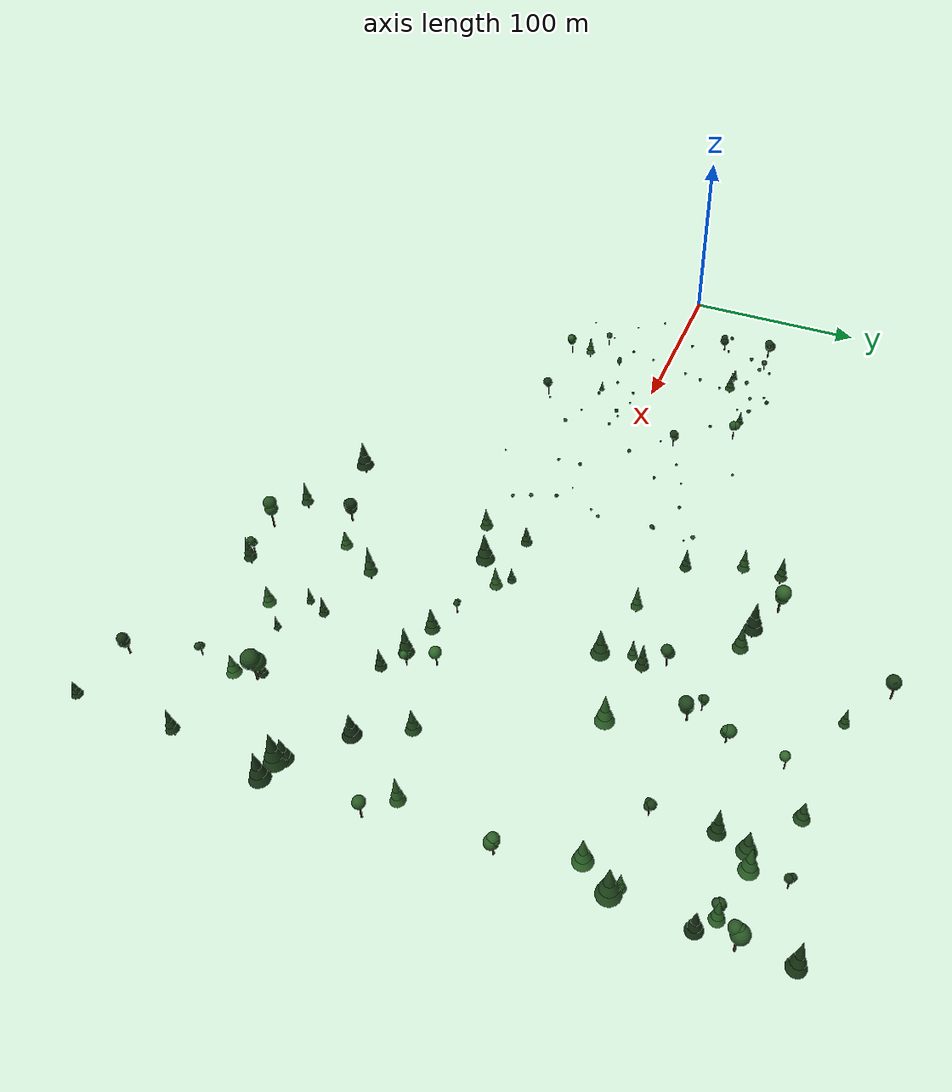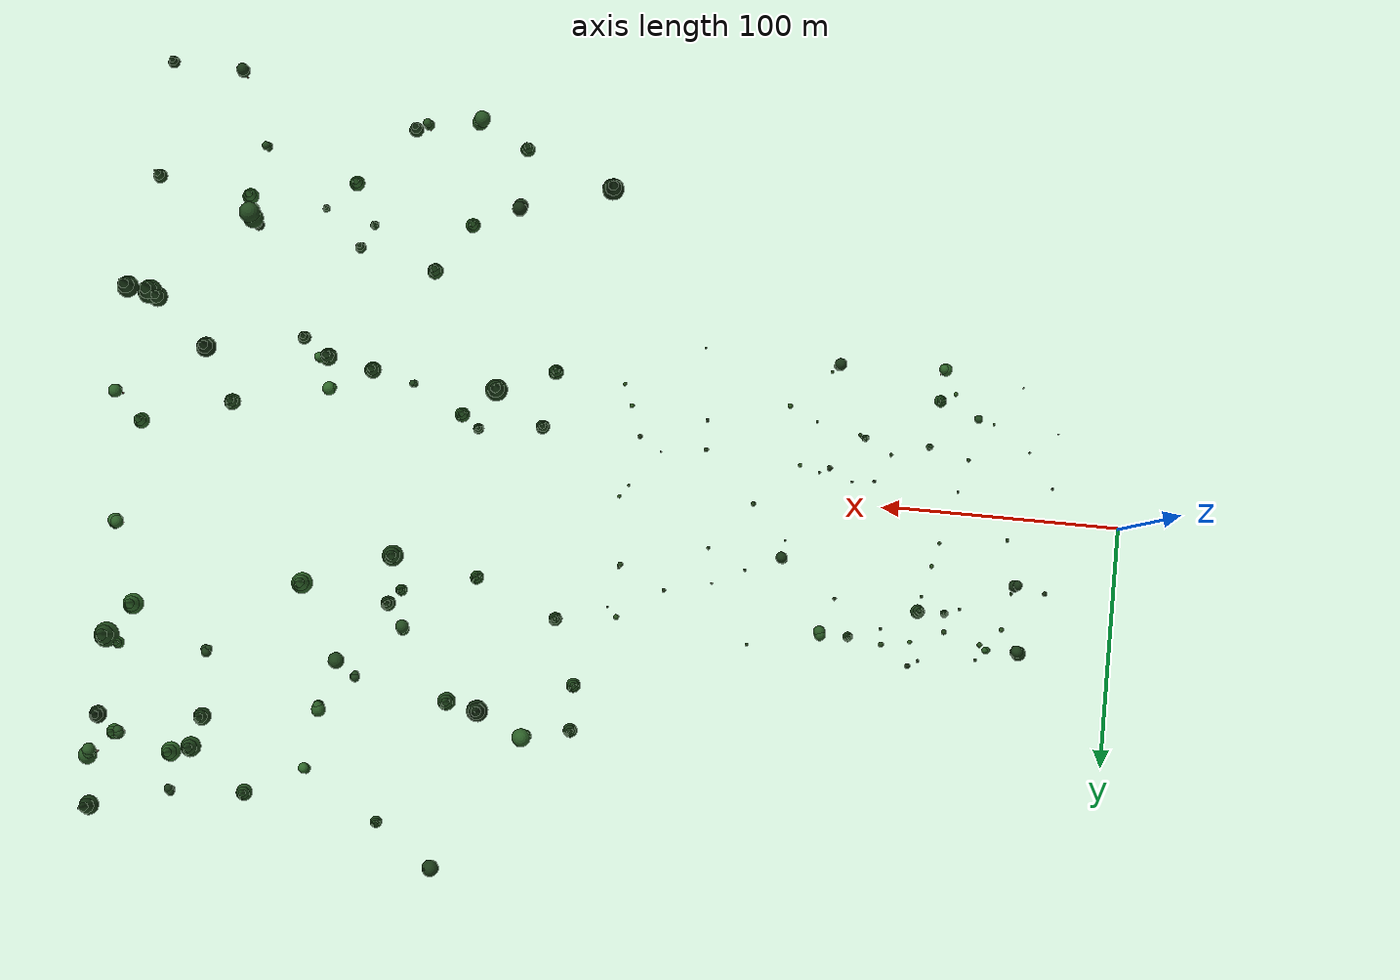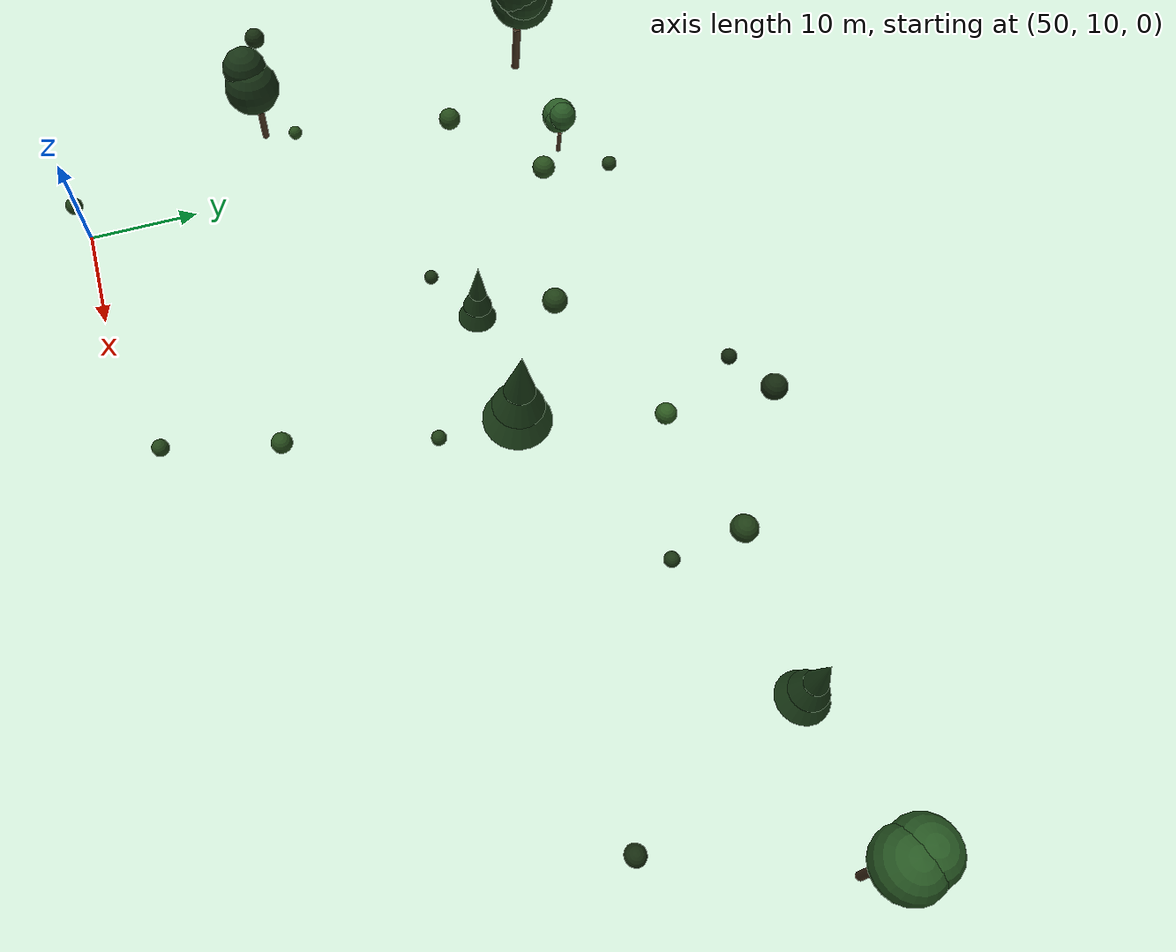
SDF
<sdf version="1.9">
 <world name="detection_world_terrain_train_ir">
  <physics type="ode">
   <max_step_size>0.004</max_step_size>
   <real_time_factor>1.0</real_time_factor>
   <real_time_update_rate>250</real_time_update_rate>
  </physics>
  <gravity>0 0 -9.8</gravity>
  <magnetic_field>6e-06 2.3e-05 -4.2e-05</magnetic_field>
  <atmosphere type="adiabatic"><temperature>288</temperature></atmosphere>
  <plugin filename="gz-sim-physics-system" name="gz::sim::systems::Physics"/>
  <plugin filename="gz-sim-user-commands-system" name="gz::sim::systems::UserCommands"/>
  <plugin filename="gz-sim-scene-broadcaster-system" name="gz::sim::systems::SceneBroadcaster"/>
  <plugin filename="gz-sim-sensors-system" name="gz::sim::systems::Sensors">
   <render_engine>ogre2</render_engine>
  </plugin>
  <plugin filename="gz-sim-imu-system" name="gz::sim::systems::Imu"/>
  <plugin filename="gz-sim-magnetometer-system" name="gz::sim::systems::Magnetometer"/>
  <plugin filename="gz-sim-air-pressure-system" name="gz::sim::systems::AirPressure"/>
  <plugin filename="gz-sim-navsat-system" name="gz::sim::systems::NavSat"/>
  <scene>
   <grid>false</grid>
   <ambient>0.4 0.4 0.4 1</ambient>
   <background>0.55 0.7 0.9 1</background>
   <shadows>true</shadows>
  </scene>
  <light name="sunUTC" type="directional">
   <pose>0 0 500 0 -0 0</pose>
   <intensity>1</intensity>
   <direction>0.001 0.625 -0.78</direction>
   <diffuse>0.904 0.904 0.904 1</diffuse>
   <specular>0.271 0.271 0.271 1</specular>
   <attenuation><range>2000</range><linear>0</linear><constant>1</constant><quadratic>0</quadratic></attenuation>
  </light>
  <model name="detection_station">
   <static>true</static>
   <link name="base">
    <pose>0 0 0.5 0 0 0</pose>
    <visual name="cabin">
     <geometry><box><size>1.2 1.2 1.0</size></box></geometry>
     <material><ambient>0.3 0.3 0.32 1</ambient><diffuse>0.3 0.3 0.32 1</diffuse></material>
    </visual>
    <collision name="cabin_col"><geometry><box><size>1.2 1.2 1.0</size></box></geometry></collision>
   </link>
   <link name="mast">
    <pose>0 0 1.75 0 0 0</pose>
    <visual name="pole">
     <geometry><cylinder><radius>0.04</radius><length>1.5</length></cylinder></geometry>
     <material><ambient>0.5 0.5 0.5 1</ambient><diffuse>0.5 0.5 0.5 1</diffuse></material>
    </visual>
   </link>
   <link name="camera_link">
    <pose>0.1 0 2.5 0 -0.15 0</pose>
    <visual name="camera_body">
     <geometry><box><size>0.12 0.08 0.08</size></box></geometry>
     <material><ambient>0.1 0.1 0.1 1</ambient><diffuse>0.1 0.1 0.1 1</diffuse></material>
    </visual>
    <sensor name="station_camera" type="camera">
     <topic>/detection_station/camera/image</topic>
     <update_rate>15</update_rate>
     <always_on>true</always_on>
     <visualize>false</visualize>
     <camera>
      <horizontal_fov>1.047</horizontal_fov>
      <image><width>1280</width><height>720</height><format>R8G8B8</format></image>
      <clip><near>0.1</near><far>1000</far></clip>
      <camera_info_topic>/detection_station/camera/camera_info</camera_info_topic>
     </camera>
    </sensor>
    <sensor name="station_thermal" type="thermal">
     <topic>/detection_station/thermal/image</topic>
     <update_rate>15</update_rate>
     <always_on>true</always_on>
     <visualize>false</visualize>
     <camera>
      <horizontal_fov>0.4189</horizontal_fov>
      <image><width>640</width><height>512</height><format>L16</format></image>
      <clip><near>0.1</near><far>1000</far></clip>
     </camera>
     <plugin filename="gz-sim-thermal-sensor-system" name="gz::sim::systems::ThermalSensor">
      <min_temp>253.15</min_temp>
      <max_temp>673.15</max_temp>
      <resolution>0.01</resolution>
     </plugin>
    </sensor>
   </link>
   <link name="mic_array_link">
    <pose>0 0.35 1.1 0 0 0</pose>
    <visual name="mic_array">
     <geometry><cylinder><radius>0.09</radius><length>0.06</length></cylinder></geometry>
     <material><ambient>0.15 0.15 0.4 1</ambient><diffuse>0.15 0.15 0.4 1</diffuse></material>
    </visual>
   </link>
   <link name="radar_link">
    <pose>0.15 -0.35 1.3 0 -0.1 0</pose>
    <visual name="radar_panel">
     <geometry><box><size>0.04 0.5 0.4</size></box></geometry>
     <material><ambient>0.6 0.6 0.62 1</ambient><diffuse>0.6 0.6 0.62 1</diffuse></material>
    </visual>
   </link>
  </model>
  <spherical_coordinates>
   <surface_model>EARTH_WGS84</surface_model>
   <world_frame_orientation>ENU</world_frame_orientation>
   <latitude_deg>47.397971057728974</latitude_deg>
   <longitude_deg>8.546163739800146</longitude_deg>
   <elevation>0</elevation>
  </spherical_coordinates>
  <model name="tree_0">
   <static>true</static>
   <pose>324.40 104.27 10.50 0 0 0.39</pose>
   <link name="link">
    <visual name="trunk">
     <pose>0 0 2.46 0 0 0</pose>
     <geometry><cylinder><radius>0.37</radius><length>4.92</length></cylinder></geometry>
     <material><ambient>0.28 0.2 0.12 1</ambient><diffuse>0.28 0.2 0.12 1</diffuse></material>
    </visual>
    <visual name="canopy0">
     <pose>0.30 -0.73 7.82 0 0 0</pose>
     <geometry><sphere><radius>2.28</radius></sphere></geometry>
     <material><ambient>0.157 0.349 0.140 1</ambient><diffuse>0.157 0.349 0.140 1</diffuse></material>
    </visual>
    <visual name="canopy1">
     <pose>0.46 -0.46 9.49 0 0 0</pose>
     <geometry><sphere><radius>2.21</radius></sphere></geometry>
     <material><ambient>0.157 0.349 0.140 1</ambient><diffuse>0.157 0.349 0.140 1</diffuse></material>
    </visual>
    <visual name="canopy2">
     <pose>0.65 0.83 9.14 0 0 0</pose>
     <geometry><sphere><radius>2.95</radius></sphere></geometry>
     <material><ambient>0.157 0.349 0.140 1</ambient><diffuse>0.157 0.349 0.140 1</diffuse></material>
    </visual>
   </link>
  </model>
  <model name="tree_1">
   <static>true</static>
   <pose>382.52 127.61 16.47 0 0 1.32</pose>
   <link name="link">
    <visual name="trunk">
     <pose>0 0 3.48 0 0 0</pose>
     <geometry><cylinder><radius>0.49</radius><length>6.96</length></cylinder></geometry>
     <material><ambient>0.28 0.2 0.12 1</ambient><diffuse>0.28 0.2 0.12 1</diffuse></material>
    </visual>
    <visual name="canopy0">
     <pose>0 0 8.95 0 0 0</pose>
     <geometry><cone><radius>4.07</radius><length>8.35</length></cone></geometry>
     <material><ambient>0.184 0.409 0.164 1</ambient><diffuse>0.184 0.409 0.164 1</diffuse></material>
    </visual>
    <visual name="canopy1">
     <pose>0 0 12.92 0 0 0</pose>
     <geometry><cone><radius>3.05</radius><length>8.35</length></cone></geometry>
     <material><ambient>0.184 0.409 0.164 1</ambient><diffuse>0.184 0.409 0.164 1</diffuse></material>
    </visual>
    <visual name="canopy2">
     <pose>0 0 16.90 0 0 0</pose>
     <geometry><cone><radius>1.83</radius><length>8.35</length></cone></geometry>
     <material><ambient>0.184 0.409 0.164 1</ambient><diffuse>0.184 0.409 0.164 1</diffuse></material>
    </visual>
   </link>
  </model>
  <model name="tree_2">
   <static>true</static>
   <pose>327.99 130.04 10.75 0 0 2.35</pose>
   <link name="link">
    <visual name="trunk">
     <pose>0 0 2.51 0 0 0</pose>
     <geometry><cylinder><radius>0.29</radius><length>5.02</length></cylinder></geometry>
     <material><ambient>0.28 0.2 0.12 1</ambient><diffuse>0.28 0.2 0.12 1</diffuse></material>
    </visual>
    <visual name="canopy0">
     <pose>-0.04 0.71 8.39 0 0 0</pose>
     <geometry><sphere><radius>2.11</radius></sphere></geometry>
     <material><ambient>0.182 0.406 0.162 1</ambient><diffuse>0.182 0.406 0.162 1</diffuse></material>
    </visual>
    <visual name="canopy1">
     <pose>0.45 0.60 7.94 0 0 0</pose>
     <geometry><sphere><radius>1.74</radius></sphere></geometry>
     <material><ambient>0.182 0.406 0.162 1</ambient><diffuse>0.182 0.406 0.162 1</diffuse></material>
    </visual>
    <visual name="canopy2">
     <pose>-0.64 0.36 9.15 0 0 0</pose>
     <geometry><sphere><radius>2.23</radius></sphere></geometry>
     <material><ambient>0.182 0.406 0.162 1</ambient><diffuse>0.182 0.406 0.162 1</diffuse></material>
    </visual>
   </link>
  </model>
  <model name="tree_3">
   <static>true</static>
   <pose>374.87 125.05 15.91 0 0 2.26</pose>
   <link name="link">
    <visual name="trunk">
     <pose>0 0 3.11 0 0 0</pose>
     <geometry><cylinder><radius>0.51</radius><length>6.23</length></cylinder></geometry>
     <material><ambient>0.28 0.2 0.12 1</ambient><diffuse>0.28 0.2 0.12 1</diffuse></material>
    </visual>
    <visual name="canopy0">
     <pose>0 0 8.01 0 0 0</pose>
     <geometry><cone><radius>4.21</radius><length>7.47</length></cone></geometry>
     <material><ambient>0.138 0.306 0.123 1</ambient><diffuse>0.138 0.306 0.123 1</diffuse></material>
    </visual>
    <visual name="canopy1">
     <pose>0 0 11.57 0 0 0</pose>
     <geometry><cone><radius>3.16</radius><length>7.47</length></cone></geometry>
     <material><ambient>0.138 0.306 0.123 1</ambient><diffuse>0.138 0.306 0.123 1</diffuse></material>
    </visual>
    <visual name="canopy2">
     <pose>0 0 15.13 0 0 0</pose>
     <geometry><cone><radius>1.89</radius><length>7.47</length></cone></geometry>
     <material><ambient>0.138 0.306 0.123 1</ambient><diffuse>0.138 0.306 0.123 1</diffuse></material>
    </visual>
   </link>
  </model>
  <model name="tree_4">
   <static>true</static>
   <pose>273.44 97.40 6.11 0 0 0.81</pose>
   <link name="link">
    <visual name="trunk">
     <pose>0 0 3.23 0 0 0</pose>
     <geometry><cylinder><radius>0.45</radius><length>6.46</length></cylinder></geometry>
     <material><ambient>0.28 0.2 0.12 1</ambient><diffuse>0.28 0.2 0.12 1</diffuse></material>
    </visual>
    <visual name="canopy0">
     <pose>0 0 8.30 0 0 0</pose>
     <geometry><cone><radius>3.77</radius><length>7.75</length></cone></geometry>
     <material><ambient>0.141 0.313 0.125 1</ambient><diffuse>0.141 0.313 0.125 1</diffuse></material>
    </visual>
    <visual name="canopy1">
     <pose>0 0 12.00 0 0 0</pose>
     <geometry><cone><radius>2.83</radius><length>7.75</length></cone></geometry>
     <material><ambient>0.141 0.313 0.125 1</ambient><diffuse>0.141 0.313 0.125 1</diffuse></material>
    </visual>
    <visual name="canopy2">
     <pose>0 0 15.69 0 0 0</pose>
     <geometry><cone><radius>1.70</radius><length>7.75</length></cone></geometry>
     <material><ambient>0.141 0.313 0.125 1</ambient><diffuse>0.141 0.313 0.125 1</diffuse></material>
    </visual>
   </link>
  </model>
  <model name="tree_5">
   <static>true</static>
   <pose>351.71 141.62 13.55 0 0 1.71</pose>
   <link name="link">
    <visual name="trunk">
     <pose>0 0 2.56 0 0 0</pose>
     <geometry><cylinder><radius>0.41</radius><length>5.13</length></cylinder></geometry>
     <material><ambient>0.28 0.2 0.12 1</ambient><diffuse>0.28 0.2 0.12 1</diffuse></material>
    </visual>
    <visual name="canopy0">
     <pose>0 0 6.59 0 0 0</pose>
     <geometry><cone><radius>3.41</radius><length>6.15</length></cone></geometry>
     <material><ambient>0.143 0.319 0.128 1</ambient><diffuse>0.143 0.319 0.128 1</diffuse></material>
    </visual>
    <visual name="canopy1">
     <pose>0 0 9.52 0 0 0</pose>
     <geometry><cone><radius>2.56</radius><length>6.15</length></cone></geometry>
     <material><ambient>0.143 0.319 0.128 1</ambient><diffuse>0.143 0.319 0.128 1</diffuse></material>
    </visual>
    <visual name="canopy2">
     <pose>0 0 12.45 0 0 0</pose>
     <geometry><cone><radius>1.53</radius><length>6.15</length></cone></geometry>
     <material><ambient>0.143 0.319 0.128 1</ambient><diffuse>0.143 0.319 0.128 1</diffuse></material>
    </visual>
   </link>
  </model>
  <model name="tree_6">
   <static>true</static>
   <pose>221.95 86.11 2.88 0 0 4.58</pose>
   <link name="link">
    <visual name="trunk">
     <pose>0 0 2.89 0 0 0</pose>
     <geometry><cylinder><radius>0.36</radius><length>5.79</length></cylinder></geometry>
     <material><ambient>0.28 0.2 0.12 1</ambient><diffuse>0.28 0.2 0.12 1</diffuse></material>
    </visual>
    <visual name="canopy0">
     <pose>0 0 7.44 0 0 0</pose>
     <geometry><cone><radius>3.01</radius><length>6.95</length></cone></geometry>
     <material><ambient>0.149 0.332 0.133 1</ambient><diffuse>0.149 0.332 0.133 1</diffuse></material>
    </visual>
    <visual name="canopy1">
     <pose>0 0 10.75 0 0 0</pose>
     <geometry><cone><radius>2.26</radius><length>6.95</length></cone></geometry>
     <material><ambient>0.149 0.332 0.133 1</ambient><diffuse>0.149 0.332 0.133 1</diffuse></material>
    </visual>
    <visual name="canopy2">
     <pose>0 0 14.06 0 0 0</pose>
     <geometry><cone><radius>1.35</radius><length>6.95</length></cone></geometry>
     <material><ambient>0.149 0.332 0.133 1</ambient><diffuse>0.149 0.332 0.133 1</diffuse></material>
    </visual>
   </link>
  </model>
  <model name="tree_7">
   <static>true</static>
   <pose>281.96 -144.49 6.29 0 0 3.37</pose>
   <link name="link">
    <visual name="trunk">
     <pose>0 0 3.98 0 0 0</pose>
     <geometry><cylinder><radius>0.44</radius><length>7.96</length></cylinder></geometry>
     <material><ambient>0.28 0.2 0.12 1</ambient><diffuse>0.28 0.2 0.12 1</diffuse></material>
    </visual>
    <visual name="canopy0">
     <pose>0.41 -0.21 16.67 0 0 0</pose>
     <geometry><sphere><radius>3.44</radius></sphere></geometry>
     <material><ambient>0.142 0.315 0.126 1</ambient><diffuse>0.142 0.315 0.126 1</diffuse></material>
    </visual>
    <visual name="canopy1">
     <pose>0.20 -0.24 13.62 0 0 0</pose>
     <geometry><sphere><radius>2.53</radius></sphere></geometry>
     <material><ambient>0.142 0.315 0.126 1</ambient><diffuse>0.142 0.315 0.126 1</diffuse></material>
    </visual>
    <visual name="canopy2">
     <pose>-0.77 -0.86 13.71 0 0 0</pose>
     <geometry><sphere><radius>3.29</radius></sphere></geometry>
     <material><ambient>0.142 0.315 0.126 1</ambient><diffuse>0.142 0.315 0.126 1</diffuse></material>
    </visual>
   </link>
  </model>
  <model name="tree_8">
   <static>true</static>
   <pose>380.99 142.86 16.07 0 0 4.55</pose>
   <link name="link">
    <visual name="trunk">
     <pose>0 0 1.87 0 0 0</pose>
     <geometry><cylinder><radius>0.30</radius><length>3.74</length></cylinder></geometry>
     <material><ambient>0.28 0.2 0.12 1</ambient><diffuse>0.28 0.2 0.12 1</diffuse></material>
    </visual>
    <visual name="canopy0">
     <pose>0.41 0.51 7.64 0 0 0</pose>
     <geometry><sphere><radius>1.86</radius></sphere></geometry>
     <material><ambient>0.091 0.202 0.081 1</ambient><diffuse>0.091 0.202 0.081 1</diffuse></material>
    </visual>
    <visual name="canopy1">
     <pose>-0.64 -0.62 7.58 0 0 0</pose>
     <geometry><sphere><radius>1.71</radius></sphere></geometry>
     <material><ambient>0.091 0.202 0.081 1</ambient><diffuse>0.091 0.202 0.081 1</diffuse></material>
    </visual>
    <visual name="canopy2">
     <pose>0.05 -0.35 6.32 0 0 0</pose>
     <geometry><sphere><radius>1.76</radius></sphere></geometry>
     <material><ambient>0.091 0.202 0.081 1</ambient><diffuse>0.091 0.202 0.081 1</diffuse></material>
    </visual>
   </link>
  </model>
  <model name="tree_9">
   <static>true</static>
   <pose>317.36 -36.46 9.45 0 0 6.08</pose>
   <link name="link">
    <visual name="trunk">
     <pose>0 0 3.11 0 0 0</pose>
     <geometry><cylinder><radius>0.43</radius><length>6.21</length></cylinder></geometry>
     <material><ambient>0.28 0.2 0.12 1</ambient><diffuse>0.28 0.2 0.12 1</diffuse></material>
    </visual>
    <visual name="canopy0">
     <pose>0 0 7.99 0 0 0</pose>
     <geometry><cone><radius>3.57</radius><length>7.46</length></cone></geometry>
     <material><ambient>0.129 0.287 0.115 1</ambient><diffuse>0.129 0.287 0.115 1</diffuse></material>
    </visual>
    <visual name="canopy1">
     <pose>0 0 11.54 0 0 0</pose>
     <geometry><cone><radius>2.68</radius><length>7.46</length></cone></geometry>
     <material><ambient>0.129 0.287 0.115 1</ambient><diffuse>0.129 0.287 0.115 1</diffuse></material>
    </visual>
    <visual name="canopy2">
     <pose>0 0 15.09 0 0 0</pose>
     <geometry><cone><radius>1.61</radius><length>7.46</length></cone></geometry>
     <material><ambient>0.129 0.287 0.115 1</ambient><diffuse>0.129 0.287 0.115 1</diffuse></material>
    </visual>
   </link>
  </model>
  <model name="tree_10">
   <static>true</static>
   <pose>370.35 -92.12 15.42 0 0 4.68</pose>
   <link name="link">
    <visual name="trunk">
     <pose>0 0 2.21 0 0 0</pose>
     <geometry><cylinder><radius>0.29</radius><length>4.43</length></cylinder></geometry>
     <material><ambient>0.28 0.2 0.12 1</ambient><diffuse>0.28 0.2 0.12 1</diffuse></material>
    </visual>
    <visual name="canopy0">
     <pose>0 0 5.69 0 0 0</pose>
     <geometry><cone><radius>2.39</radius><length>5.31</length></cone></geometry>
     <material><ambient>0.084 0.187 0.075 1</ambient><diffuse>0.084 0.187 0.075 1</diffuse></material>
    </visual>
    <visual name="canopy1">
     <pose>0 0 8.22 0 0 0</pose>
     <geometry><cone><radius>1.79</radius><length>5.31</length></cone></geometry>
     <material><ambient>0.084 0.187 0.075 1</ambient><diffuse>0.084 0.187 0.075 1</diffuse></material>
    </visual>
    <visual name="canopy2">
     <pose>0 0 10.75 0 0 0</pose>
     <geometry><cone><radius>1.08</radius><length>5.31</length></cone></geometry>
     <material><ambient>0.084 0.187 0.075 1</ambient><diffuse>0.084 0.187 0.075 1</diffuse></material>
    </visual>
   </link>
  </model>
  <model name="tree_11">
   <static>true</static>
   <pose>333.58 -26.29 11.20 0 0 4.42</pose>
   <link name="link">
    <visual name="trunk">
     <pose>0 0 2.56 0 0 0</pose>
     <geometry><cylinder><radius>0.36</radius><length>5.11</length></cylinder></geometry>
     <material><ambient>0.28 0.2 0.12 1</ambient><diffuse>0.28 0.2 0.12 1</diffuse></material>
    </visual>
    <visual name="canopy0">
     <pose>0.10 0.20 9.37 0 0 0</pose>
     <geometry><sphere><radius>2.86</radius></sphere></geometry>
     <material><ambient>0.181 0.403 0.161 1</ambient><diffuse>0.181 0.403 0.161 1</diffuse></material>
    </visual>
    <visual name="canopy1">
     <pose>0.46 -0.36 9.33 0 0 0</pose>
     <geometry><sphere><radius>2.43</radius></sphere></geometry>
     <material><ambient>0.181 0.403 0.161 1</ambient><diffuse>0.181 0.403 0.161 1</diffuse></material>
    </visual>
    <visual name="canopy2">
     <pose>0.03 0.04 8.73 0 0 0</pose>
     <geometry><sphere><radius>2.41</radius></sphere></geometry>
     <material><ambient>0.181 0.403 0.161 1</ambient><diffuse>0.181 0.403 0.161 1</diffuse></material>
    </visual>
   </link>
  </model>
  <model name="tree_12">
   <static>true</static>
   <pose>373.00 -17.21 16.43 0 0 0.08</pose>
   <link name="link">
    <visual name="trunk">
     <pose>0 0 2.99 0 0 0</pose>
     <geometry><cylinder><radius>0.42</radius><length>5.97</length></cylinder></geometry>
     <material><ambient>0.28 0.2 0.12 1</ambient><diffuse>0.28 0.2 0.12 1</diffuse></material>
    </visual>
    <visual name="canopy0">
     <pose>0 0 7.68 0 0 0</pose>
     <geometry><cone><radius>3.46</radius><length>7.17</length></cone></geometry>
     <material><ambient>0.132 0.294 0.118 1</ambient><diffuse>0.132 0.294 0.118 1</diffuse></material>
    </visual>
    <visual name="canopy1">
     <pose>0 0 11.09 0 0 0</pose>
     <geometry><cone><radius>2.60</radius><length>7.17</length></cone></geometry>
     <material><ambient>0.132 0.294 0.118 1</ambient><diffuse>0.132 0.294 0.118 1</diffuse></material>
    </visual>
    <visual name="canopy2">
     <pose>0 0 14.50 0 0 0</pose>
     <geometry><cone><radius>1.56</radius><length>7.17</length></cone></geometry>
     <material><ambient>0.132 0.294 0.118 1</ambient><diffuse>0.132 0.294 0.118 1</diffuse></material>
    </visual>
   </link>
  </model>
  <model name="tree_13">
   <static>true</static>
   <pose>272.69 165.85 6.06 0 0 3.37</pose>
   <link name="link">
    <visual name="trunk">
     <pose>0 0 2.90 0 0 0</pose>
     <geometry><cylinder><radius>0.44</radius><length>5.79</length></cylinder></geometry>
     <material><ambient>0.28 0.2 0.12 1</ambient><diffuse>0.28 0.2 0.12 1</diffuse></material>
    </visual>
    <visual name="canopy0">
     <pose>-0.51 0.04 11.99 0 0 0</pose>
     <geometry><sphere><radius>2.22</radius></sphere></geometry>
     <material><ambient>0.104 0.231 0.092 1</ambient><diffuse>0.104 0.231 0.092 1</diffuse></material>
    </visual>
    <visual name="canopy1">
     <pose>-0.06 0.89 11.63 0 0 0</pose>
     <geometry><sphere><radius>3.45</radius></sphere></geometry>
     <material><ambient>0.104 0.231 0.092 1</ambient><diffuse>0.104 0.231 0.092 1</diffuse></material>
    </visual>
    <visual name="canopy2">
     <pose>-0.88 0.89 12.56 0 0 0</pose>
     <geometry><sphere><radius>2.22</radius></sphere></geometry>
     <material><ambient>0.104 0.231 0.092 1</ambient><diffuse>0.104 0.231 0.092 1</diffuse></material>
    </visual>
   </link>
  </model>
  <model name="tree_14">
   <static>true</static>
   <pose>371.86 -94.50 15.38 0 0 2.13</pose>
   <link name="link">
    <visual name="trunk">
     <pose>0 0 3.83 0 0 0</pose>
     <geometry><cylinder><radius>0.59</radius><length>7.67</length></cylinder></geometry>
     <material><ambient>0.28 0.2 0.12 1</ambient><diffuse>0.28 0.2 0.12 1</diffuse></material>
    </visual>
    <visual name="canopy0">
     <pose>-1.30 0.12 13.08 0 0 0</pose>
     <geometry><sphere><radius>3.86</radius></sphere></geometry>
     <material><ambient>0.127 0.283 0.113 1</ambient><diffuse>0.127 0.283 0.113 1</diffuse></material>
    </visual>
    <visual name="canopy1">
     <pose>-0.68 -0.45 15.03 0 0 0</pose>
     <geometry><sphere><radius>4.34</radius></sphere></geometry>
     <material><ambient>0.127 0.283 0.113 1</ambient><diffuse>0.127 0.283 0.113 1</diffuse></material>
    </visual>
    <visual name="canopy2">
     <pose>1.40 -0.28 12.09 0 0 0</pose>
     <geometry><sphere><radius>4.22</radius></sphere></geometry>
     <material><ambient>0.127 0.283 0.113 1</ambient><diffuse>0.127 0.283 0.113 1</diffuse></material>
    </visual>
   </link>
  </model>
  <model name="tree_15">
   <static>true</static>
   <pose>371.53 112.39 15.48 0 0 2.10</pose>
   <link name="link">
    <visual name="trunk">
     <pose>0 0 3.54 0 0 0</pose>
     <geometry><cylinder><radius>0.44</radius><length>7.08</length></cylinder></geometry>
     <material><ambient>0.28 0.2 0.12 1</ambient><diffuse>0.28 0.2 0.12 1</diffuse></material>
    </visual>
    <visual name="canopy0">
     <pose>0 0 9.10 0 0 0</pose>
     <geometry><cone><radius>3.70</radius><length>8.50</length></cone></geometry>
     <material><ambient>0.116 0.257 0.103 1</ambient><diffuse>0.116 0.257 0.103 1</diffuse></material>
    </visual>
    <visual name="canopy1">
     <pose>0 0 13.15 0 0 0</pose>
     <geometry><cone><radius>2.77</radius><length>8.50</length></cone></geometry>
     <material><ambient>0.116 0.257 0.103 1</ambient><diffuse>0.116 0.257 0.103 1</diffuse></material>
    </visual>
    <visual name="canopy2">
     <pose>0 0 17.20 0 0 0</pose>
     <geometry><cone><radius>1.66</radius><length>8.50</length></cone></geometry>
     <material><ambient>0.116 0.257 0.103 1</ambient><diffuse>0.116 0.257 0.103 1</diffuse></material>
    </visual>
   </link>
  </model>
  <model name="tree_16">
   <static>true</static>
   <pose>327.68 -87.29 10.52 0 0 4.28</pose>
   <link name="link">
    <visual name="trunk">
     <pose>0 0 2.44 0 0 0</pose>
     <geometry><cylinder><radius>0.28</radius><length>4.89</length></cylinder></geometry>
     <material><ambient>0.28 0.2 0.12 1</ambient><diffuse>0.28 0.2 0.12 1</diffuse></material>
    </visual>
    <visual name="canopy0">
     <pose>0 0 6.28 0 0 0</pose>
     <geometry><cone><radius>2.37</radius><length>5.87</length></cone></geometry>
     <material><ambient>0.108 0.240 0.096 1</ambient><diffuse>0.108 0.240 0.096 1</diffuse></material>
    </visual>
    <visual name="canopy1">
     <pose>0 0 9.08 0 0 0</pose>
     <geometry><cone><radius>1.78</radius><length>5.87</length></cone></geometry>
     <material><ambient>0.108 0.240 0.096 1</ambient><diffuse>0.108 0.240 0.096 1</diffuse></material>
    </visual>
    <visual name="canopy2">
     <pose>0 0 11.87 0 0 0</pose>
     <geometry><cone><radius>1.07</radius><length>5.87</length></cone></geometry>
     <material><ambient>0.108 0.240 0.096 1</ambient><diffuse>0.108 0.240 0.096 1</diffuse></material>
    </visual>
   </link>
  </model>
  <model name="tree_17">
   <static>true</static>
   <pose>282.10 -101.90 5.74 0 0 0.95</pose>
   <link name="link">
    <visual name="trunk">
     <pose>0 0 2.27 0 0 0</pose>
     <geometry><cylinder><radius>0.37</radius><length>4.55</length></cylinder></geometry>
     <material><ambient>0.28 0.2 0.12 1</ambient><diffuse>0.28 0.2 0.12 1</diffuse></material>
    </visual>
    <visual name="canopy0">
     <pose>0 0 5.85 0 0 0</pose>
     <geometry><cone><radius>3.10</radius><length>5.46</length></cone></geometry>
     <material><ambient>0.166 0.369 0.148 1</ambient><diffuse>0.166 0.369 0.148 1</diffuse></material>
    </visual>
    <visual name="canopy1">
     <pose>0 0 8.44 0 0 0</pose>
     <geometry><cone><radius>2.33</radius><length>5.46</length></cone></geometry>
     <material><ambient>0.166 0.369 0.148 1</ambient><diffuse>0.166 0.369 0.148 1</diffuse></material>
    </visual>
    <visual name="canopy2">
     <pose>0 0 11.04 0 0 0</pose>
     <geometry><cone><radius>1.40</radius><length>5.46</length></cone></geometry>
     <material><ambient>0.166 0.369 0.148 1</ambient><diffuse>0.166 0.369 0.148 1</diffuse></material>
    </visual>
   </link>
  </model>
  <model name="tree_18">
   <static>true</static>
   <pose>278.76 -21.80 5.20 0 0 0.97</pose>
   <link name="link">
    <visual name="trunk">
     <pose>0 0 2.70 0 0 0</pose>
     <geometry><cylinder><radius>0.37</radius><length>5.40</length></cylinder></geometry>
     <material><ambient>0.28 0.2 0.12 1</ambient><diffuse>0.28 0.2 0.12 1</diffuse></material>
    </visual>
    <visual name="canopy0">
     <pose>0 0 6.95 0 0 0</pose>
     <geometry><cone><radius>3.12</radius><length>6.48</length></cone></geometry>
     <material><ambient>0.163 0.362 0.145 1</ambient><diffuse>0.163 0.362 0.145 1</diffuse></material>
    </visual>
    <visual name="canopy1">
     <pose>0 0 10.03 0 0 0</pose>
     <geometry><cone><radius>2.34</radius><length>6.48</length></cone></geometry>
     <material><ambient>0.163 0.362 0.145 1</ambient><diffuse>0.163 0.362 0.145 1</diffuse></material>
    </visual>
    <visual name="canopy2">
     <pose>0 0 13.12 0 0 0</pose>
     <geometry><cone><radius>1.40</radius><length>6.48</length></cone></geometry>
     <material><ambient>0.163 0.362 0.145 1</ambient><diffuse>0.163 0.362 0.145 1</diffuse></material>
    </visual>
   </link>
  </model>
  <model name="tree_19">
   <static>true</static>
   <pose>331.84 -114.08 10.98 0 0 6.01</pose>
   <link name="link">
    <visual name="trunk">
     <pose>0 0 2.53 0 0 0</pose>
     <geometry><cylinder><radius>0.39</radius><length>5.05</length></cylinder></geometry>
     <material><ambient>0.28 0.2 0.12 1</ambient><diffuse>0.28 0.2 0.12 1</diffuse></material>
    </visual>
    <visual name="canopy0">
     <pose>0 0 6.50 0 0 0</pose>
     <geometry><cone><radius>3.24</radius><length>6.06</length></cone></geometry>
     <material><ambient>0.176 0.391 0.157 1</ambient><diffuse>0.176 0.391 0.157 1</diffuse></material>
    </visual>
    <visual name="canopy1">
     <pose>0 0 9.39 0 0 0</pose>
     <geometry><cone><radius>2.43</radius><length>6.06</length></cone></geometry>
     <material><ambient>0.176 0.391 0.157 1</ambient><diffuse>0.176 0.391 0.157 1</diffuse></material>
    </visual>
    <visual name="canopy2">
     <pose>0 0 12.27 0 0 0</pose>
     <geometry><cone><radius>1.46</radius><length>6.06</length></cone></geometry>
     <material><ambient>0.176 0.391 0.157 1</ambient><diffuse>0.176 0.391 0.157 1</diffuse></material>
    </visual>
   </link>
  </model>
  <model name="tree_20">
   <static>true</static>
   <pose>301.43 39.69 7.95 0 0 2.02</pose>
   <link name="link">
    <visual name="trunk">
     <pose>0 0 3.49 0 0 0</pose>
     <geometry><cylinder><radius>0.53</radius><length>6.99</length></cylinder></geometry>
     <material><ambient>0.28 0.2 0.12 1</ambient><diffuse>0.28 0.2 0.12 1</diffuse></material>
    </visual>
    <visual name="canopy0">
     <pose>0 0 8.98 0 0 0</pose>
     <geometry><cone><radius>4.44</radius><length>8.38</length></cone></geometry>
     <material><ambient>0.127 0.282 0.113 1</ambient><diffuse>0.127 0.282 0.113 1</diffuse></material>
    </visual>
    <visual name="canopy1">
     <pose>0 0 12.98 0 0 0</pose>
     <geometry><cone><radius>3.33</radius><length>8.38</length></cone></geometry>
     <material><ambient>0.127 0.282 0.113 1</ambient><diffuse>0.127 0.282 0.113 1</diffuse></material>
    </visual>
    <visual name="canopy2">
     <pose>0 0 16.97 0 0 0</pose>
     <geometry><cone><radius>2.00</radius><length>8.38</length></cone></geometry>
     <material><ambient>0.127 0.282 0.113 1</ambient><diffuse>0.127 0.282 0.113 1</diffuse></material>
    </visual>
   </link>
  </model>
  <model name="tree_21">
   <static>true</static>
   <pose>371.61 85.12 15.74 0 0 2.02</pose>
   <link name="link">
    <visual name="trunk">
     <pose>0 0 2.46 0 0 0</pose>
     <geometry><cylinder><radius>0.30</radius><length>4.91</length></cylinder></geometry>
     <material><ambient>0.28 0.2 0.12 1</ambient><diffuse>0.28 0.2 0.12 1</diffuse></material>
    </visual>
    <visual name="canopy0">
     <pose>-0.47 -0.75 8.15 0 0 0</pose>
     <geometry><sphere><radius>1.95</radius></sphere></geometry>
     <material><ambient>0.108 0.240 0.096 1</ambient><diffuse>0.108 0.240 0.096 1</diffuse></material>
    </visual>
    <visual name="canopy1">
     <pose>-0.10 0.59 9.05 0 0 0</pose>
     <geometry><sphere><radius>1.66</radius></sphere></geometry>
     <material><ambient>0.108 0.240 0.096 1</ambient><diffuse>0.108 0.240 0.096 1</diffuse></material>
    </visual>
    <visual name="canopy2">
     <pose>0.65 -0.65 8.92 0 0 0</pose>
     <geometry><sphere><radius>2.18</radius></sphere></geometry>
     <material><ambient>0.108 0.240 0.096 1</ambient><diffuse>0.108 0.240 0.096 1</diffuse></material>
    </visual>
   </link>
  </model>
  <model name="tree_22">
   <static>true</static>
   <pose>412.79 82.79 21.17 0 0 0.90</pose>
   <link name="link">
    <visual name="trunk">
     <pose>0 0 3.87 0 0 0</pose>
     <geometry><cylinder><radius>0.62</radius><length>7.73</length></cylinder></geometry>
     <material><ambient>0.28 0.2 0.12 1</ambient><diffuse>0.28 0.2 0.12 1</diffuse></material>
    </visual>
    <visual name="canopy0">
     <pose>0 0 9.94 0 0 0</pose>
     <geometry><cone><radius>5.16</radius><length>9.28</length></cone></geometry>
     <material><ambient>0.137 0.303 0.121 1</ambient><diffuse>0.137 0.303 0.121 1</diffuse></material>
    </visual>
    <visual name="canopy1">
     <pose>0 0 14.36 0 0 0</pose>
     <geometry><cone><radius>3.87</radius><length>9.28</length></cone></geometry>
     <material><ambient>0.137 0.303 0.121 1</ambient><diffuse>0.137 0.303 0.121 1</diffuse></material>
    </visual>
    <visual name="canopy2">
     <pose>0 0 18.77 0 0 0</pose>
     <geometry><cone><radius>2.32</radius><length>9.28</length></cone></geometry>
     <material><ambient>0.137 0.303 0.121 1</ambient><diffuse>0.137 0.303 0.121 1</diffuse></material>
    </visual>
   </link>
  </model>
  <model name="tree_23">
   <static>true</static>
   <pose>240.82 108.10 3.84 0 0 3.57</pose>
   <link name="link">
    <visual name="trunk">
     <pose>0 0 3.35 0 0 0</pose>
     <geometry><cylinder><radius>0.51</radius><length>6.70</length></cylinder></geometry>
     <material><ambient>0.28 0.2 0.12 1</ambient><diffuse>0.28 0.2 0.12 1</diffuse></material>
    </visual>
    <visual name="canopy0">
     <pose>-0.67 -0.73 14.69 0 0 0</pose>
     <geometry><sphere><radius>3.80</radius></sphere></geometry>
     <material><ambient>0.167 0.370 0.148 1</ambient><diffuse>0.167 0.370 0.148 1</diffuse></material>
    </visual>
    <visual name="canopy1">
     <pose>-0.16 -0.59 10.91 0 0 0</pose>
     <geometry><sphere><radius>3.15</radius></sphere></geometry>
     <material><ambient>0.167 0.370 0.148 1</ambient><diffuse>0.167 0.370 0.148 1</diffuse></material>
    </visual>
    <visual name="canopy2">
     <pose>1.04 -0.76 12.05 0 0 0</pose>
     <geometry><sphere><radius>2.60</radius></sphere></geometry>
     <material><ambient>0.167 0.370 0.148 1</ambient><diffuse>0.167 0.370 0.148 1</diffuse></material>
    </visual>
   </link>
  </model>
  <model name="tree_24">
   <static>true</static>
   <pose>232.02 59.46 2.93 0 0 5.61</pose>
   <link name="link">
    <visual name="trunk">
     <pose>0 0 2.79 0 0 0</pose>
     <geometry><cylinder><radius>0.35</radius><length>5.57</length></cylinder></geometry>
     <material><ambient>0.28 0.2 0.12 1</ambient><diffuse>0.28 0.2 0.12 1</diffuse></material>
    </visual>
    <visual name="canopy0">
     <pose>0 0 7.17 0 0 0</pose>
     <geometry><cone><radius>2.88</radius><length>6.69</length></cone></geometry>
     <material><ambient>0.114 0.253 0.101 1</ambient><diffuse>0.114 0.253 0.101 1</diffuse></material>
    </visual>
    <visual name="canopy1">
     <pose>0 0 10.35 0 0 0</pose>
     <geometry><cone><radius>2.16</radius><length>6.69</length></cone></geometry>
     <material><ambient>0.114 0.253 0.101 1</ambient><diffuse>0.114 0.253 0.101 1</diffuse></material>
    </visual>
    <visual name="canopy2">
     <pose>0 0 13.54 0 0 0</pose>
     <geometry><cone><radius>1.30</radius><length>6.69</length></cone></geometry>
     <material><ambient>0.114 0.253 0.101 1</ambient><diffuse>0.114 0.253 0.101 1</diffuse></material>
    </visual>
   </link>
  </model>
  <model name="tree_25">
   <static>true</static>
   <pose>408.15 85.67 20.79 0 0 5.92</pose>
   <link name="link">
    <visual name="trunk">
     <pose>0 0 2.26 0 0 0</pose>
     <geometry><cylinder><radius>0.29</radius><length>4.52</length></cylinder></geometry>
     <material><ambient>0.28 0.2 0.12 1</ambient><diffuse>0.28 0.2 0.12 1</diffuse></material>
    </visual>
    <visual name="canopy0">
     <pose>0 0 5.81 0 0 0</pose>
     <geometry><cone><radius>2.44</radius><length>5.42</length></cone></geometry>
     <material><ambient>0.176 0.390 0.156 1</ambient><diffuse>0.176 0.390 0.156 1</diffuse></material>
    </visual>
    <visual name="canopy1">
     <pose>0 0 8.39 0 0 0</pose>
     <geometry><cone><radius>1.83</radius><length>5.42</length></cone></geometry>
     <material><ambient>0.176 0.390 0.156 1</ambient><diffuse>0.176 0.390 0.156 1</diffuse></material>
    </visual>
    <visual name="canopy2">
     <pose>0 0 10.98 0 0 0</pose>
     <geometry><cone><radius>1.10</radius><length>5.42</length></cone></geometry>
     <material><ambient>0.176 0.390 0.156 1</ambient><diffuse>0.176 0.390 0.156 1</diffuse></material>
    </visual>
   </link>
  </model>
  <model name="tree_26">
   <static>true</static>
   <pose>266.00 45.36 4.84 0 0 4.91</pose>
   <link name="link">
    <visual name="trunk">
     <pose>0 0 2.87 0 0 0</pose>
     <geometry><cylinder><radius>0.35</radius><length>5.73</length></cylinder></geometry>
     <material><ambient>0.28 0.2 0.12 1</ambient><diffuse>0.28 0.2 0.12 1</diffuse></material>
    </visual>
    <visual name="canopy0">
     <pose>0 0 7.37 0 0 0</pose>
     <geometry><cone><radius>2.88</radius><length>6.88</length></cone></geometry>
     <material><ambient>0.159 0.353 0.141 1</ambient><diffuse>0.159 0.353 0.141 1</diffuse></material>
    </visual>
    <visual name="canopy1">
     <pose>0 0 10.65 0 0 0</pose>
     <geometry><cone><radius>2.16</radius><length>6.88</length></cone></geometry>
     <material><ambient>0.159 0.353 0.141 1</ambient><diffuse>0.159 0.353 0.141 1</diffuse></material>
    </visual>
    <visual name="canopy2">
     <pose>0 0 13.92 0 0 0</pose>
     <geometry><cone><radius>1.30</radius><length>6.88</length></cone></geometry>
     <material><ambient>0.159 0.353 0.141 1</ambient><diffuse>0.159 0.353 0.141 1</diffuse></material>
    </visual>
   </link>
  </model>
  <model name="tree_27">
   <static>true</static>
   <pose>407.89 -5.38 22.88 0 0 4.82</pose>
   <link name="link">
    <visual name="trunk">
     <pose>0 0 3.33 0 0 0</pose>
     <geometry><cylinder><radius>0.39</radius><length>6.67</length></cylinder></geometry>
     <material><ambient>0.28 0.2 0.12 1</ambient><diffuse>0.28 0.2 0.12 1</diffuse></material>
    </visual>
    <visual name="canopy0">
     <pose>0 0 8.57 0 0 0</pose>
     <geometry><cone><radius>3.25</radius><length>8.00</length></cone></geometry>
     <material><ambient>0.176 0.391 0.156 1</ambient><diffuse>0.176 0.391 0.156 1</diffuse></material>
    </visual>
    <visual name="canopy1">
     <pose>0 0 12.38 0 0 0</pose>
     <geometry><cone><radius>2.44</radius><length>8.00</length></cone></geometry>
     <material><ambient>0.176 0.391 0.156 1</ambient><diffuse>0.176 0.391 0.156 1</diffuse></material>
    </visual>
    <visual name="canopy2">
     <pose>0 0 16.19 0 0 0</pose>
     <geometry><cone><radius>1.46</radius><length>8.00</length></cone></geometry>
     <material><ambient>0.176 0.391 0.156 1</ambient><diffuse>0.176 0.391 0.156 1</diffuse></material>
    </visual>
   </link>
  </model>
  <model name="tree_28">
   <static>true</static>
   <pose>265.55 -33.37 4.22 0 0 5.97</pose>
   <link name="link">
    <visual name="trunk">
     <pose>0 0 3.84 0 0 0</pose>
     <geometry><cylinder><radius>0.57</radius><length>7.67</length></cylinder></geometry>
     <material><ambient>0.28 0.2 0.12 1</ambient><diffuse>0.28 0.2 0.12 1</diffuse></material>
    </visual>
    <visual name="canopy0">
     <pose>0 0 9.87 0 0 0</pose>
     <geometry><cone><radius>4.72</radius><length>9.21</length></cone></geometry>
     <material><ambient>0.107 0.237 0.095 1</ambient><diffuse>0.107 0.237 0.095 1</diffuse></material>
    </visual>
    <visual name="canopy1">
     <pose>0 0 14.25 0 0 0</pose>
     <geometry><cone><radius>3.54</radius><length>9.21</length></cone></geometry>
     <material><ambient>0.107 0.237 0.095 1</ambient><diffuse>0.107 0.237 0.095 1</diffuse></material>
    </visual>
    <visual name="canopy2">
     <pose>0 0 18.64 0 0 0</pose>
     <geometry><cone><radius>2.13</radius><length>9.21</length></cone></geometry>
     <material><ambient>0.107 0.237 0.095 1</ambient><diffuse>0.107 0.237 0.095 1</diffuse></material>
    </visual>
   </link>
  </model>
  <model name="tree_29">
   <static>true</static>
   <pose>405.98 121.65 19.24 0 0 3.02</pose>
   <link name="link">
    <visual name="trunk">
     <pose>0 0 2.91 0 0 0</pose>
     <geometry><cylinder><radius>0.38</radius><length>5.82</length></cylinder></geometry>
     <material><ambient>0.28 0.2 0.12 1</ambient><diffuse>0.28 0.2 0.12 1</diffuse></material>
    </visual>
    <visual name="canopy0">
     <pose>0 0 7.48 0 0 0</pose>
     <geometry><cone><radius>3.20</radius><length>6.98</length></cone></geometry>
     <material><ambient>0.187 0.415 0.166 1</ambient><diffuse>0.187 0.415 0.166 1</diffuse></material>
    </visual>
    <visual name="canopy1">
     <pose>0 0 10.81 0 0 0</pose>
     <geometry><cone><radius>2.40</radius><length>6.98</length></cone></geometry>
     <material><ambient>0.187 0.415 0.166 1</ambient><diffuse>0.187 0.415 0.166 1</diffuse></material>
    </visual>
    <visual name="canopy2">
     <pose>0 0 14.13 0 0 0</pose>
     <geometry><cone><radius>1.44</radius><length>6.98</length></cone></geometry>
     <material><ambient>0.187 0.415 0.166 1</ambient><diffuse>0.187 0.415 0.166 1</diffuse></material>
    </visual>
   </link>
  </model>
  <model name="tree_30">
   <static>true</static>
   <pose>411.90 -107.45 21.19 0 0 0.23</pose>
   <link name="link">
    <visual name="trunk">
     <pose>0 0 2.91 0 0 0</pose>
     <geometry><cylinder><radius>0.35</radius><length>5.81</length></cylinder></geometry>
     <material><ambient>0.28 0.2 0.12 1</ambient><diffuse>0.28 0.2 0.12 1</diffuse></material>
    </visual>
    <visual name="canopy0">
     <pose>0 0 7.47 0 0 0</pose>
     <geometry><cone><radius>2.92</radius><length>6.98</length></cone></geometry>
     <material><ambient>0.109 0.242 0.097 1</ambient><diffuse>0.109 0.242 0.097 1</diffuse></material>
    </visual>
    <visual name="canopy1">
     <pose>0 0 10.80 0 0 0</pose>
     <geometry><cone><radius>2.19</radius><length>6.98</length></cone></geometry>
     <material><ambient>0.109 0.242 0.097 1</ambient><diffuse>0.109 0.242 0.097 1</diffuse></material>
    </visual>
    <visual name="canopy2">
     <pose>0 0 14.12 0 0 0</pose>
     <geometry><cone><radius>1.31</radius><length>6.98</length></cone></geometry>
     <material><ambient>0.109 0.242 0.097 1</ambient><diffuse>0.109 0.242 0.097 1</diffuse></material>
    </visual>
   </link>
  </model>
  <model name="tree_31">
   <static>true</static>
   <pose>244.88 -20.02 3.01 0 0 1.96</pose>
   <link name="link">
    <visual name="trunk">
     <pose>0 0 2.48 0 0 0</pose>
     <geometry><cylinder><radius>0.35</radius><length>4.95</length></cylinder></geometry>
     <material><ambient>0.28 0.2 0.12 1</ambient><diffuse>0.28 0.2 0.12 1</diffuse></material>
    </visual>
    <visual name="canopy0">
     <pose>0 0 6.37 0 0 0</pose>
     <geometry><cone><radius>2.96</radius><length>5.94</length></cone></geometry>
     <material><ambient>0.109 0.242 0.097 1</ambient><diffuse>0.109 0.242 0.097 1</diffuse></material>
    </visual>
    <visual name="canopy1">
     <pose>0 0 9.20 0 0 0</pose>
     <geometry><cone><radius>2.22</radius><length>5.94</length></cone></geometry>
     <material><ambient>0.109 0.242 0.097 1</ambient><diffuse>0.109 0.242 0.097 1</diffuse></material>
    </visual>
    <visual name="canopy2">
     <pose>0 0 12.03 0 0 0</pose>
     <geometry><cone><radius>1.33</radius><length>5.94</length></cone></geometry>
     <material><ambient>0.109 0.242 0.097 1</ambient><diffuse>0.109 0.242 0.097 1</diffuse></material>
    </visual>
   </link>
  </model>
  <model name="tree_32">
   <static>true</static>
   <pose>295.68 -80.49 7.30 0 0 3.36</pose>
   <link name="link">
    <visual name="trunk">
     <pose>0 0 3.65 0 0 0</pose>
     <geometry><cylinder><radius>0.41</radius><length>7.31</length></cylinder></geometry>
     <material><ambient>0.28 0.2 0.12 1</ambient><diffuse>0.28 0.2 0.12 1</diffuse></material>
    </visual>
    <visual name="canopy0">
     <pose>0 0 9.39 0 0 0</pose>
     <geometry><cone><radius>3.39</radius><length>8.77</length></cone></geometry>
     <material><ambient>0.139 0.309 0.124 1</ambient><diffuse>0.139 0.309 0.124 1</diffuse></material>
    </visual>
    <visual name="canopy1">
     <pose>0 0 13.57 0 0 0</pose>
     <geometry><cone><radius>2.54</radius><length>8.77</length></cone></geometry>
     <material><ambient>0.139 0.309 0.124 1</ambient><diffuse>0.139 0.309 0.124 1</diffuse></material>
    </visual>
    <visual name="canopy2">
     <pose>0 0 17.74 0 0 0</pose>
     <geometry><cone><radius>1.53</radius><length>8.77</length></cone></geometry>
     <material><ambient>0.139 0.309 0.124 1</ambient><diffuse>0.139 0.309 0.124 1</diffuse></material>
    </visual>
   </link>
  </model>
  <model name="tree_33">
   <static>true</static>
   <pose>403.65 69.39 20.39 0 0 4.82</pose>
   <link name="link">
    <visual name="trunk">
     <pose>0 0 3.26 0 0 0</pose>
     <geometry><cylinder><radius>0.52</radius><length>6.52</length></cylinder></geometry>
     <material><ambient>0.28 0.2 0.12 1</ambient><diffuse>0.28 0.2 0.12 1</diffuse></material>
    </visual>
    <visual name="canopy0">
     <pose>0 0 8.38 0 0 0</pose>
     <geometry><cone><radius>4.32</radius><length>7.82</length></cone></geometry>
     <material><ambient>0.184 0.408 0.163 1</ambient><diffuse>0.184 0.408 0.163 1</diffuse></material>
    </visual>
    <visual name="canopy1">
     <pose>0 0 12.11 0 0 0</pose>
     <geometry><cone><radius>3.24</radius><length>7.82</length></cone></geometry>
     <material><ambient>0.184 0.408 0.163 1</ambient><diffuse>0.184 0.408 0.163 1</diffuse></material>
    </visual>
    <visual name="canopy2">
     <pose>0 0 15.83 0 0 0</pose>
     <geometry><cone><radius>1.94</radius><length>7.82</length></cone></geometry>
     <material><ambient>0.184 0.408 0.163 1</ambient><diffuse>0.184 0.408 0.163 1</diffuse></material>
    </visual>
   </link>
  </model>
  <model name="tree_34">
   <static>true</static>
   <pose>241.52 -43.54 2.79 0 0 6.15</pose>
   <link name="link">
    <visual name="trunk">
     <pose>0 0 2.56 0 0 0</pose>
     <geometry><cylinder><radius>0.39</radius><length>5.11</length></cylinder></geometry>
     <material><ambient>0.28 0.2 0.12 1</ambient><diffuse>0.28 0.2 0.12 1</diffuse></material>
    </visual>
    <visual name="canopy0">
     <pose>0 0 6.57 0 0 0</pose>
     <geometry><cone><radius>3.22</radius><length>6.14</length></cone></geometry>
     <material><ambient>0.134 0.298 0.119 1</ambient><diffuse>0.134 0.298 0.119 1</diffuse></material>
    </visual>
    <visual name="canopy1">
     <pose>0 0 9.50 0 0 0</pose>
     <geometry><cone><radius>2.42</radius><length>6.14</length></cone></geometry>
     <material><ambient>0.134 0.298 0.119 1</ambient><diffuse>0.134 0.298 0.119 1</diffuse></material>
    </visual>
    <visual name="canopy2">
     <pose>0 0 12.42 0 0 0</pose>
     <geometry><cone><radius>1.45</radius><length>6.14</length></cone></geometry>
     <material><ambient>0.134 0.298 0.119 1</ambient><diffuse>0.134 0.298 0.119 1</diffuse></material>
    </visual>
   </link>
  </model>
  <model name="tree_35">
   <static>true</static>
   <pose>221.57 104.69 2.98 0 0 3.84</pose>
   <link name="link">
    <visual name="trunk">
     <pose>0 0 3.02 0 0 0</pose>
     <geometry><cylinder><radius>0.36</radius><length>6.04</length></cylinder></geometry>
     <material><ambient>0.28 0.2 0.12 1</ambient><diffuse>0.28 0.2 0.12 1</diffuse></material>
    </visual>
    <visual name="canopy0">
     <pose>0 0 7.77 0 0 0</pose>
     <geometry><cone><radius>2.97</radius><length>7.25</length></cone></geometry>
     <material><ambient>0.122 0.272 0.109 1</ambient><diffuse>0.122 0.272 0.109 1</diffuse></material>
    </visual>
    <visual name="canopy1">
     <pose>0 0 11.22 0 0 0</pose>
     <geometry><cone><radius>2.23</radius><length>7.25</length></cone></geometry>
     <material><ambient>0.122 0.272 0.109 1</ambient><diffuse>0.122 0.272 0.109 1</diffuse></material>
    </visual>
    <visual name="canopy2">
     <pose>0 0 14.67 0 0 0</pose>
     <geometry><cone><radius>1.34</radius><length>7.25</length></cone></geometry>
     <material><ambient>0.122 0.272 0.109 1</ambient><diffuse>0.122 0.272 0.109 1</diffuse></material>
    </visual>
   </link>
  </model>
  <model name="tree_36">
   <static>true</static>
   <pose>411.76 -156.10 21.31 0 0 1.24</pose>
   <link name="link">
    <visual name="trunk">
     <pose>0 0 2.02 0 0 0</pose>
     <geometry><cylinder><radius>0.30</radius><length>4.04</length></cylinder></geometry>
     <material><ambient>0.28 0.2 0.12 1</ambient><diffuse>0.28 0.2 0.12 1</diffuse></material>
    </visual>
    <visual name="canopy0">
     <pose>0 0 5.19 0 0 0</pose>
     <geometry><cone><radius>2.53</radius><length>4.84</length></cone></geometry>
     <material><ambient>0.097 0.214 0.086 1</ambient><diffuse>0.097 0.214 0.086 1</diffuse></material>
    </visual>
    <visual name="canopy1">
     <pose>0 0 7.50 0 0 0</pose>
     <geometry><cone><radius>1.90</radius><length>4.84</length></cone></geometry>
     <material><ambient>0.097 0.214 0.086 1</ambient><diffuse>0.097 0.214 0.086 1</diffuse></material>
    </visual>
    <visual name="canopy2">
     <pose>0 0 9.80 0 0 0</pose>
     <geometry><cone><radius>1.14</radius><length>4.84</length></cone></geometry>
     <material><ambient>0.097 0.214 0.086 1</ambient><diffuse>0.097 0.214 0.086 1</diffuse></material>
    </visual>
   </link>
  </model>
  <model name="tree_37">
   <static>true</static>
   <pose>381.76 -153.99 17.22 0 0 2.03</pose>
   <link name="link">
    <visual name="trunk">
     <pose>0 0 2.41 0 0 0</pose>
     <geometry><cylinder><radius>0.40</radius><length>4.81</length></cylinder></geometry>
     <material><ambient>0.28 0.2 0.12 1</ambient><diffuse>0.28 0.2 0.12 1</diffuse></material>
    </visual>
    <visual name="canopy0">
     <pose>-0.80 -0.05 8.63 0 0 0</pose>
     <geometry><sphere><radius>2.72</radius></sphere></geometry>
     <material><ambient>0.092 0.205 0.082 1</ambient><diffuse>0.092 0.205 0.082 1</diffuse></material>
    </visual>
    <visual name="canopy1">
     <pose>-0.39 -0.33 7.62 0 0 0</pose>
     <geometry><sphere><radius>2.08</radius></sphere></geometry>
     <material><ambient>0.092 0.205 0.082 1</ambient><diffuse>0.092 0.205 0.082 1</diffuse></material>
    </visual>
    <visual name="canopy2">
     <pose>-0.98 -0.08 10.58 0 0 0</pose>
     <geometry><sphere><radius>2.60</radius></sphere></geometry>
     <material><ambient>0.092 0.205 0.082 1</ambient><diffuse>0.092 0.205 0.082 1</diffuse></material>
    </visual>
   </link>
  </model>
  <model name="tree_38">
   <static>true</static>
   <pose>311.85 90.34 9.37 0 0 1.85</pose>
   <link name="link">
    <visual name="trunk">
     <pose>0 0 1.98 0 0 0</pose>
     <geometry><cylinder><radius>0.29</radius><length>3.96</length></cylinder></geometry>
     <material><ambient>0.28 0.2 0.12 1</ambient><diffuse>0.28 0.2 0.12 1</diffuse></material>
    </visual>
    <visual name="canopy0">
     <pose>0.62 0.32 7.88 0 0 0</pose>
     <geometry><sphere><radius>1.99</radius></sphere></geometry>
     <material><ambient>0.113 0.251 0.101 1</ambient><diffuse>0.113 0.251 0.101 1</diffuse></material>
    </visual>
    <visual name="canopy1">
     <pose>0.38 -0.62 7.13 0 0 0</pose>
     <geometry><sphere><radius>1.47</radius></sphere></geometry>
     <material><ambient>0.113 0.251 0.101 1</ambient><diffuse>0.113 0.251 0.101 1</diffuse></material>
    </visual>
    <visual name="canopy2">
     <pose>-0.50 0.61 7.83 0 0 0</pose>
     <geometry><sphere><radius>1.60</radius></sphere></geometry>
     <material><ambient>0.113 0.251 0.101 1</ambient><diffuse>0.113 0.251 0.101 1</diffuse></material>
    </visual>
   </link>
  </model>
  <model name="tree_39">
   <static>true</static>
   <pose>303.89 -140.99 8.26 0 0 4.96</pose>
   <link name="link">
    <visual name="trunk">
     <pose>0 0 2.68 0 0 0</pose>
     <geometry><cylinder><radius>0.30</radius><length>5.37</length></cylinder></geometry>
     <material><ambient>0.28 0.2 0.12 1</ambient><diffuse>0.28 0.2 0.12 1</diffuse></material>
    </visual>
    <visual name="canopy0">
     <pose>-0.13 0.40 9.44 0 0 0</pose>
     <geometry><sphere><radius>1.72</radius></sphere></geometry>
     <material><ambient>0.137 0.304 0.121 1</ambient><diffuse>0.137 0.304 0.121 1</diffuse></material>
    </visual>
    <visual name="canopy1">
     <pose>0.00 -0.14 8.93 0 0 0</pose>
     <geometry><sphere><radius>2.16</radius></sphere></geometry>
     <material><ambient>0.137 0.304 0.121 1</ambient><diffuse>0.137 0.304 0.121 1</diffuse></material>
    </visual>
    <visual name="canopy2">
     <pose>0.55 0.50 10.96 0 0 0</pose>
     <geometry><sphere><radius>1.93</radius></sphere></geometry>
     <material><ambient>0.137 0.304 0.121 1</ambient><diffuse>0.137 0.304 0.121 1</diffuse></material>
    </visual>
   </link>
  </model>
  <model name="tree_40">
   <static>true</static>
   <pose>262.20 -136.35 4.75 0 0 5.10</pose>
   <link name="link">
    <visual name="trunk">
     <pose>0 0 3.05 0 0 0</pose>
     <geometry><cylinder><radius>0.37</radius><length>6.10</length></cylinder></geometry>
     <material><ambient>0.28 0.2 0.12 1</ambient><diffuse>0.28 0.2 0.12 1</diffuse></material>
    </visual>
    <visual name="canopy0">
     <pose>0 0 7.84 0 0 0</pose>
     <geometry><cone><radius>3.08</radius><length>7.32</length></cone></geometry>
     <material><ambient>0.128 0.285 0.114 1</ambient><diffuse>0.128 0.285 0.114 1</diffuse></material>
    </visual>
    <visual name="canopy1">
     <pose>0 0 11.33 0 0 0</pose>
     <geometry><cone><radius>2.31</radius><length>7.32</length></cone></geometry>
     <material><ambient>0.128 0.285 0.114 1</ambient><diffuse>0.128 0.285 0.114 1</diffuse></material>
    </visual>
    <visual name="canopy2">
     <pose>0 0 14.81 0 0 0</pose>
     <geometry><cone><radius>1.39</radius><length>7.32</length></cone></geometry>
     <material><ambient>0.128 0.285 0.114 1</ambient><diffuse>0.128 0.285 0.114 1</diffuse></material>
    </visual>
   </link>
  </model>
  <model name="tree_41">
   <static>true</static>
   <pose>343.53 -102.35 12.22 0 0 4.47</pose>
   <link name="link">
    <visual name="trunk">
     <pose>0 0 1.76 0 0 0</pose>
     <geometry><cylinder><radius>0.20</radius><length>3.53</length></cylinder></geometry>
     <material><ambient>0.28 0.2 0.12 1</ambient><diffuse>0.28 0.2 0.12 1</diffuse></material>
    </visual>
    <visual name="canopy0">
     <pose>0 0 4.54 0 0 0</pose>
     <geometry><cone><radius>1.65</radius><length>4.23</length></cone></geometry>
     <material><ambient>0.109 0.243 0.097 1</ambient><diffuse>0.109 0.243 0.097 1</diffuse></material>
    </visual>
    <visual name="canopy1">
     <pose>0 0 6.55 0 0 0</pose>
     <geometry><cone><radius>1.24</radius><length>4.23</length></cone></geometry>
     <material><ambient>0.109 0.243 0.097 1</ambient><diffuse>0.109 0.243 0.097 1</diffuse></material>
    </visual>
    <visual name="canopy2">
     <pose>0 0 8.57 0 0 0</pose>
     <geometry><cone><radius>0.74</radius><length>4.23</length></cone></geometry>
     <material><ambient>0.109 0.243 0.097 1</ambient><diffuse>0.109 0.243 0.097 1</diffuse></material>
    </visual>
   </link>
  </model>
  <model name="tree_42">
   <static>true</static>
   <pose>385.89 -38.65 18.24 0 0 3.95</pose>
   <link name="link">
    <visual name="trunk">
     <pose>0 0 3.12 0 0 0</pose>
     <geometry><cylinder><radius>0.50</radius><length>6.24</length></cylinder></geometry>
     <material><ambient>0.28 0.2 0.12 1</ambient><diffuse>0.28 0.2 0.12 1</diffuse></material>
    </visual>
    <visual name="canopy0">
     <pose>0 0 8.03 0 0 0</pose>
     <geometry><cone><radius>4.21</radius><length>7.49</length></cone></geometry>
     <material><ambient>0.083 0.184 0.073 1</ambient><diffuse>0.083 0.184 0.073 1</diffuse></material>
    </visual>
    <visual name="canopy1">
     <pose>0 0 11.59 0 0 0</pose>
     <geometry><cone><radius>3.16</radius><length>7.49</length></cone></geometry>
     <material><ambient>0.083 0.184 0.073 1</ambient><diffuse>0.083 0.184 0.073 1</diffuse></material>
    </visual>
    <visual name="canopy2">
     <pose>0 0 15.16 0 0 0</pose>
     <geometry><cone><radius>1.89</radius><length>7.49</length></cone></geometry>
     <material><ambient>0.083 0.184 0.073 1</ambient><diffuse>0.083 0.184 0.073 1</diffuse></material>
    </visual>
   </link>
  </model>
  <model name="tree_43">
   <static>true</static>
   <pose>419.62 -59.90 23.00 0 0 4.94</pose>
   <link name="link">
    <visual name="trunk">
     <pose>0 0 3.74 0 0 0</pose>
     <geometry><cylinder><radius>0.55</radius><length>7.47</length></cylinder></geometry>
     <material><ambient>0.28 0.2 0.12 1</ambient><diffuse>0.28 0.2 0.12 1</diffuse></material>
    </visual>
    <visual name="canopy0">
     <pose>0 0 9.61 0 0 0</pose>
     <geometry><cone><radius>4.55</radius><length>8.97</length></cone></geometry>
     <material><ambient>0.100 0.221 0.089 1</ambient><diffuse>0.100 0.221 0.089 1</diffuse></material>
    </visual>
    <visual name="canopy1">
     <pose>0 0 13.88 0 0 0</pose>
     <geometry><cone><radius>3.42</radius><length>8.97</length></cone></geometry>
     <material><ambient>0.100 0.221 0.089 1</ambient><diffuse>0.100 0.221 0.089 1</diffuse></material>
    </visual>
    <visual name="canopy2">
     <pose>0 0 18.15 0 0 0</pose>
     <geometry><cone><radius>2.05</radius><length>8.97</length></cone></geometry>
     <material><ambient>0.100 0.221 0.089 1</ambient><diffuse>0.100 0.221 0.089 1</diffuse></material>
    </visual>
   </link>
  </model>
  <model name="tree_44">
   <static>true</static>
   <pose>337.18 54.46 11.42 0 0 0.69</pose>
   <link name="link">
    <visual name="trunk">
     <pose>0 0 3.77 0 0 0</pose>
     <geometry><cylinder><radius>0.53</radius><length>7.55</length></cylinder></geometry>
     <material><ambient>0.28 0.2 0.12 1</ambient><diffuse>0.28 0.2 0.12 1</diffuse></material>
    </visual>
    <visual name="canopy0">
     <pose>0 0 9.70 0 0 0</pose>
     <geometry><cone><radius>4.44</radius><length>9.06</length></cone></geometry>
     <material><ambient>0.181 0.402 0.161 1</ambient><diffuse>0.181 0.402 0.161 1</diffuse></material>
    </visual>
    <visual name="canopy1">
     <pose>0 0 14.01 0 0 0</pose>
     <geometry><cone><radius>3.33</radius><length>9.06</length></cone></geometry>
     <material><ambient>0.181 0.402 0.161 1</ambient><diffuse>0.181 0.402 0.161 1</diffuse></material>
    </visual>
    <visual name="canopy2">
     <pose>0 0 18.33 0 0 0</pose>
     <geometry><cone><radius>2.00</radius><length>9.06</length></cone></geometry>
     <material><ambient>0.181 0.402 0.161 1</ambient><diffuse>0.181 0.402 0.161 1</diffuse></material>
    </visual>
   </link>
  </model>
  <model name="tree_45">
   <static>true</static>
   <pose>224.77 -123.22 2.44 0 0 0.05</pose>
   <link name="link">
    <visual name="trunk">
     <pose>0 0 3.51 0 0 0</pose>
     <geometry><cylinder><radius>0.56</radius><length>7.02</length></cylinder></geometry>
     <material><ambient>0.28 0.2 0.12 1</ambient><diffuse>0.28 0.2 0.12 1</diffuse></material>
    </visual>
    <visual name="canopy0">
     <pose>0 0 9.03 0 0 0</pose>
     <geometry><cone><radius>4.68</radius><length>8.43</length></cone></geometry>
     <material><ambient>0.082 0.182 0.073 1</ambient><diffuse>0.082 0.182 0.073 1</diffuse></material>
    </visual>
    <visual name="canopy1">
     <pose>0 0 13.04 0 0 0</pose>
     <geometry><cone><radius>3.51</radius><length>8.43</length></cone></geometry>
     <material><ambient>0.082 0.182 0.073 1</ambient><diffuse>0.082 0.182 0.073 1</diffuse></material>
    </visual>
    <visual name="canopy2">
     <pose>0 0 17.05 0 0 0</pose>
     <geometry><cone><radius>2.11</radius><length>8.43</length></cone></geometry>
     <material><ambient>0.082 0.182 0.073 1</ambient><diffuse>0.082 0.182 0.073 1</diffuse></material>
    </visual>
   </link>
  </model>
  <model name="tree_46">
   <static>true</static>
   <pose>296.51 53.48 7.83 0 0 3.81</pose>
   <link name="link">
    <visual name="trunk">
     <pose>0 0 2.44 0 0 0</pose>
     <geometry><cylinder><radius>0.29</radius><length>4.87</length></cylinder></geometry>
     <material><ambient>0.28 0.2 0.12 1</ambient><diffuse>0.28 0.2 0.12 1</diffuse></material>
    </visual>
    <visual name="canopy0">
     <pose>0 0 6.26 0 0 0</pose>
     <geometry><cone><radius>2.45</radius><length>5.85</length></cone></geometry>
     <material><ambient>0.158 0.351 0.140 1</ambient><diffuse>0.158 0.351 0.140 1</diffuse></material>
    </visual>
    <visual name="canopy1">
     <pose>0 0 9.05 0 0 0</pose>
     <geometry><cone><radius>1.84</radius><length>5.85</length></cone></geometry>
     <material><ambient>0.158 0.351 0.140 1</ambient><diffuse>0.158 0.351 0.140 1</diffuse></material>
    </visual>
    <visual name="canopy2">
     <pose>0 0 11.83 0 0 0</pose>
     <geometry><cone><radius>1.10</radius><length>5.85</length></cone></geometry>
     <material><ambient>0.158 0.351 0.140 1</ambient><diffuse>0.158 0.351 0.140 1</diffuse></material>
    </visual>
   </link>
  </model>
  <model name="tree_47">
   <static>true</static>
   <pose>410.52 -58.78 21.58 0 0 4.58</pose>
   <link name="link">
    <visual name="trunk">
     <pose>0 0 4.11 0 0 0</pose>
     <geometry><cylinder><radius>0.61</radius><length>8.21</length></cylinder></geometry>
     <material><ambient>0.28 0.2 0.12 1</ambient><diffuse>0.28 0.2 0.12 1</diffuse></material>
    </visual>
    <visual name="canopy0">
     <pose>0 0 10.56 0 0 0</pose>
     <geometry><cone><radius>5.07</radius><length>9.86</length></cone></geometry>
     <material><ambient>0.109 0.243 0.097 1</ambient><diffuse>0.109 0.243 0.097 1</diffuse></material>
    </visual>
    <visual name="canopy1">
     <pose>0 0 15.26 0 0 0</pose>
     <geometry><cone><radius>3.80</radius><length>9.86</length></cone></geometry>
     <material><ambient>0.109 0.243 0.097 1</ambient><diffuse>0.109 0.243 0.097 1</diffuse></material>
    </visual>
    <visual name="canopy2">
     <pose>0 0 19.95 0 0 0</pose>
     <geometry><cone><radius>2.28</radius><length>9.86</length></cone></geometry>
     <material><ambient>0.109 0.243 0.097 1</ambient><diffuse>0.109 0.243 0.097 1</diffuse></material>
    </visual>
   </link>
  </model>
  <model name="tree_48">
   <static>true</static>
   <pose>309.45 -139.53 8.89 0 0 4.54</pose>
   <link name="link">
    <visual name="trunk">
     <pose>0 0 2.97 0 0 0</pose>
     <geometry><cylinder><radius>0.38</radius><length>5.94</length></cylinder></geometry>
     <material><ambient>0.28 0.2 0.12 1</ambient><diffuse>0.28 0.2 0.12 1</diffuse></material>
    </visual>
    <visual name="canopy0">
     <pose>0 0 7.64 0 0 0</pose>
     <geometry><cone><radius>3.14</radius><length>7.13</length></cone></geometry>
     <material><ambient>0.109 0.242 0.097 1</ambient><diffuse>0.109 0.242 0.097 1</diffuse></material>
    </visual>
    <visual name="canopy1">
     <pose>0 0 11.03 0 0 0</pose>
     <geometry><cone><radius>2.35</radius><length>7.13</length></cone></geometry>
     <material><ambient>0.109 0.242 0.097 1</ambient><diffuse>0.109 0.242 0.097 1</diffuse></material>
    </visual>
    <visual name="canopy2">
     <pose>0 0 14.43 0 0 0</pose>
     <geometry><cone><radius>1.41</radius><length>7.13</length></cone></geometry>
     <material><ambient>0.109 0.242 0.097 1</ambient><diffuse>0.109 0.242 0.097 1</diffuse></material>
    </visual>
   </link>
  </model>
  <model name="tree_49">
   <static>true</static>
   <pose>271.55 -16.67 4.78 0 0 1.02</pose>
   <link name="link">
    <visual name="trunk">
     <pose>0 0 1.77 0 0 0</pose>
     <geometry><cylinder><radius>0.27</radius><length>3.54</length></cylinder></geometry>
     <material><ambient>0.28 0.2 0.12 1</ambient><diffuse>0.28 0.2 0.12 1</diffuse></material>
    </visual>
    <visual name="canopy0">
     <pose>0 0 4.55 0 0 0</pose>
     <geometry><cone><radius>2.27</radius><length>4.25</length></cone></geometry>
     <material><ambient>0.110 0.244 0.098 1</ambient><diffuse>0.110 0.244 0.098 1</diffuse></material>
    </visual>
    <visual name="canopy1">
     <pose>0 0 6.57 0 0 0</pose>
     <geometry><cone><radius>1.70</radius><length>4.25</length></cone></geometry>
     <material><ambient>0.110 0.244 0.098 1</ambient><diffuse>0.110 0.244 0.098 1</diffuse></material>
    </visual>
    <visual name="canopy2">
     <pose>0 0 8.59 0 0 0</pose>
     <geometry><cone><radius>1.02</radius><length>4.25</length></cone></geometry>
     <material><ambient>0.110 0.244 0.098 1</ambient><diffuse>0.110 0.244 0.098 1</diffuse></material>
    </visual>
   </link>
  </model>
  <model name="tree_50">
   <static>true</static>
   <pose>322.90 -97.52 9.82 0 0 2.05</pose>
   <link name="link">
    <visual name="trunk">
     <pose>0 0 2.03 0 0 0</pose>
     <geometry><cylinder><radius>0.23</radius><length>4.06</length></cylinder></geometry>
     <material><ambient>0.28 0.2 0.12 1</ambient><diffuse>0.28 0.2 0.12 1</diffuse></material>
    </visual>
    <visual name="canopy0">
     <pose>0 0 5.22 0 0 0</pose>
     <geometry><cone><radius>1.89</radius><length>4.87</length></cone></geometry>
     <material><ambient>0.119 0.265 0.106 1</ambient><diffuse>0.119 0.265 0.106 1</diffuse></material>
    </visual>
    <visual name="canopy1">
     <pose>0 0 7.53 0 0 0</pose>
     <geometry><cone><radius>1.42</radius><length>4.87</length></cone></geometry>
     <material><ambient>0.119 0.265 0.106 1</ambient><diffuse>0.119 0.265 0.106 1</diffuse></material>
    </visual>
    <visual name="canopy2">
     <pose>0 0 9.85 0 0 0</pose>
     <geometry><cone><radius>0.85</radius><length>4.87</length></cone></geometry>
     <material><ambient>0.119 0.265 0.106 1</ambient><diffuse>0.119 0.265 0.106 1</diffuse></material>
    </visual>
   </link>
  </model>
  <model name="tree_51">
   <static>true</static>
   <pose>261.96 -110.51 4.35 0 0 1.78</pose>
   <link name="link">
    <visual name="trunk">
     <pose>0 0 3.16 0 0 0</pose>
     <geometry><cylinder><radius>0.45</radius><length>6.32</length></cylinder></geometry>
     <material><ambient>0.28 0.2 0.12 1</ambient><diffuse>0.28 0.2 0.12 1</diffuse></material>
    </visual>
    <visual name="canopy0">
     <pose>0.96 -1.06 13.38 0 0 0</pose>
     <geometry><sphere><radius>3.12</radius></sphere></geometry>
     <material><ambient>0.082 0.182 0.073 1</ambient><diffuse>0.082 0.182 0.073 1</diffuse></material>
    </visual>
    <visual name="canopy1">
     <pose>-0.20 -0.37 12.38 0 0 0</pose>
     <geometry><sphere><radius>3.03</radius></sphere></geometry>
     <material><ambient>0.082 0.182 0.073 1</ambient><diffuse>0.082 0.182 0.073 1</diffuse></material>
    </visual>
    <visual name="canopy2">
     <pose>0.77 -1.00 10.34 0 0 0</pose>
     <geometry><sphere><radius>3.08</radius></sphere></geometry>
     <material><ambient>0.082 0.182 0.073 1</ambient><diffuse>0.082 0.182 0.073 1</diffuse></material>
    </visual>
   </link>
  </model>
  <model name="tree_52">
   <static>true</static>
   <pose>336.01 -39.85 11.65 0 0 4.67</pose>
   <link name="link">
    <visual name="trunk">
     <pose>0 0 3.77 0 0 0</pose>
     <geometry><cylinder><radius>0.45</radius><length>7.54</length></cylinder></geometry>
     <material><ambient>0.28 0.2 0.12 1</ambient><diffuse>0.28 0.2 0.12 1</diffuse></material>
    </visual>
    <visual name="canopy0">
     <pose>0 0 9.69 0 0 0</pose>
     <geometry><cone><radius>3.77</radius><length>9.04</length></cone></geometry>
     <material><ambient>0.117 0.260 0.104 1</ambient><diffuse>0.117 0.260 0.104 1</diffuse></material>
    </visual>
    <visual name="canopy1">
     <pose>0 0 14.00 0 0 0</pose>
     <geometry><cone><radius>2.83</radius><length>9.04</length></cone></geometry>
     <material><ambient>0.117 0.260 0.104 1</ambient><diffuse>0.117 0.260 0.104 1</diffuse></material>
    </visual>
    <visual name="canopy2">
     <pose>0 0 18.30 0 0 0</pose>
     <geometry><cone><radius>1.70</radius><length>9.04</length></cone></geometry>
     <material><ambient>0.117 0.260 0.104 1</ambient><diffuse>0.117 0.260 0.104 1</diffuse></material>
    </visual>
   </link>
  </model>
  <model name="tree_53">
   <static>true</static>
   <pose>402.80 121.19 18.92 0 0 4.94</pose>
   <link name="link">
    <visual name="trunk">
     <pose>0 0 2.53 0 0 0</pose>
     <geometry><cylinder><radius>0.31</radius><length>5.07</length></cylinder></geometry>
     <material><ambient>0.28 0.2 0.12 1</ambient><diffuse>0.28 0.2 0.12 1</diffuse></material>
    </visual>
    <visual name="canopy0">
     <pose>0.51 0.23 10.22 0 0 0</pose>
     <geometry><sphere><radius>2.19</radius></sphere></geometry>
     <material><ambient>0.131 0.290 0.116 1</ambient><diffuse>0.131 0.290 0.116 1</diffuse></material>
    </visual>
    <visual name="canopy1">
     <pose>-0.44 0.10 9.51 0 0 0</pose>
     <geometry><sphere><radius>2.35</radius></sphere></geometry>
     <material><ambient>0.131 0.290 0.116 1</ambient><diffuse>0.131 0.290 0.116 1</diffuse></material>
    </visual>
    <visual name="canopy2">
     <pose>-0.30 0.07 10.25 0 0 0</pose>
     <geometry><sphere><radius>2.19</radius></sphere></geometry>
     <material><ambient>0.131 0.290 0.116 1</ambient><diffuse>0.131 0.290 0.116 1</diffuse></material>
    </visual>
   </link>
  </model>
  <model name="tree_54">
   <static>true</static>
   <pose>369.52 -124.71 15.27 0 0 5.31</pose>
   <link name="link">
    <visual name="trunk">
     <pose>0 0 1.84 0 0 0</pose>
     <geometry><cylinder><radius>0.28</radius><length>3.68</length></cylinder></geometry>
     <material><ambient>0.28 0.2 0.12 1</ambient><diffuse>0.28 0.2 0.12 1</diffuse></material>
    </visual>
    <visual name="canopy0">
     <pose>-0.55 -0.19 6.09 0 0 0</pose>
     <geometry><sphere><radius>1.55</radius></sphere></geometry>
     <material><ambient>0.114 0.253 0.101 1</ambient><diffuse>0.114 0.253 0.101 1</diffuse></material>
    </visual>
    <visual name="canopy1">
     <pose>0.64 0.43 6.76 0 0 0</pose>
     <geometry><sphere><radius>1.78</radius></sphere></geometry>
     <material><ambient>0.114 0.253 0.101 1</ambient><diffuse>0.114 0.253 0.101 1</diffuse></material>
    </visual>
    <visual name="canopy2">
     <pose>0.14 -0.25 6.14 0 0 0</pose>
     <geometry><sphere><radius>1.73</radius></sphere></geometry>
     <material><ambient>0.114 0.253 0.101 1</ambient><diffuse>0.114 0.253 0.101 1</diffuse></material>
    </visual>
   </link>
  </model>
  <model name="tree_55">
   <static>true</static>
   <pose>412.09 36.69 22.36 0 0 1.73</pose>
   <link name="link">
    <visual name="trunk">
     <pose>0 0 2.78 0 0 0</pose>
     <geometry><cylinder><radius>0.42</radius><length>5.55</length></cylinder></geometry>
     <material><ambient>0.28 0.2 0.12 1</ambient><diffuse>0.28 0.2 0.12 1</diffuse></material>
    </visual>
    <visual name="canopy0">
     <pose>0.85 -0.65 10.80 0 0 0</pose>
     <geometry><sphere><radius>2.21</radius></sphere></geometry>
     <material><ambient>0.168 0.374 0.150 1</ambient><diffuse>0.168 0.374 0.150 1</diffuse></material>
    </visual>
    <visual name="canopy1">
     <pose>0.17 -0.06 11.07 0 0 0</pose>
     <geometry><sphere><radius>2.78</radius></sphere></geometry>
     <material><ambient>0.168 0.374 0.150 1</ambient><diffuse>0.168 0.374 0.150 1</diffuse></material>
    </visual>
    <visual name="canopy2">
     <pose>-0.33 -0.76 10.00 0 0 0</pose>
     <geometry><sphere><radius>3.09</radius></sphere></geometry>
     <material><ambient>0.168 0.374 0.150 1</ambient><diffuse>0.168 0.374 0.150 1</diffuse></material>
    </visual>
   </link>
  </model>
  <model name="tree_56">
   <static>true</static>
   <pose>413.11 115.19 20.19 0 0 4.84</pose>
   <link name="link">
    <visual name="trunk">
     <pose>0 0 2.86 0 0 0</pose>
     <geometry><cylinder><radius>0.44</radius><length>5.72</length></cylinder></geometry>
     <material><ambient>0.28 0.2 0.12 1</ambient><diffuse>0.28 0.2 0.12 1</diffuse></material>
    </visual>
    <visual name="canopy0">
     <pose>0 0 7.35 0 0 0</pose>
     <geometry><cone><radius>3.66</radius><length>6.86</length></cone></geometry>
     <material><ambient>0.082 0.182 0.073 1</ambient><diffuse>0.082 0.182 0.073 1</diffuse></material>
    </visual>
    <visual name="canopy1">
     <pose>0 0 10.62 0 0 0</pose>
     <geometry><cone><radius>2.74</radius><length>6.86</length></cone></geometry>
     <material><ambient>0.082 0.182 0.073 1</ambient><diffuse>0.082 0.182 0.073 1</diffuse></material>
    </visual>
    <visual name="canopy2">
     <pose>0 0 13.88 0 0 0</pose>
     <geometry><cone><radius>1.65</radius><length>6.86</length></cone></geometry>
     <material><ambient>0.082 0.182 0.073 1</ambient><diffuse>0.082 0.182 0.073 1</diffuse></material>
    </visual>
   </link>
  </model>
  <model name="tree_57">
   <static>true</static>
   <pose>301.34 59.48 8.20 0 0 3.85</pose>
   <link name="link">
    <visual name="trunk">
     <pose>0 0 3.34 0 0 0</pose>
     <geometry><cylinder><radius>0.38</radius><length>6.68</length></cylinder></geometry>
     <material><ambient>0.28 0.2 0.12 1</ambient><diffuse>0.28 0.2 0.12 1</diffuse></material>
    </visual>
    <visual name="canopy0">
     <pose>0 0 8.59 0 0 0</pose>
     <geometry><cone><radius>3.14</radius><length>8.02</length></cone></geometry>
     <material><ambient>0.112 0.248 0.099 1</ambient><diffuse>0.112 0.248 0.099 1</diffuse></material>
    </visual>
    <visual name="canopy1">
     <pose>0 0 12.41 0 0 0</pose>
     <geometry><cone><radius>2.36</radius><length>8.02</length></cone></geometry>
     <material><ambient>0.112 0.248 0.099 1</ambient><diffuse>0.112 0.248 0.099 1</diffuse></material>
    </visual>
    <visual name="canopy2">
     <pose>0 0 16.23 0 0 0</pose>
     <geometry><cone><radius>1.41</radius><length>8.02</length></cone></geometry>
     <material><ambient>0.112 0.248 0.099 1</ambient><diffuse>0.112 0.248 0.099 1</diffuse></material>
    </visual>
   </link>
  </model>
  <model name="tree_58">
   <static>true</static>
   <pose>346.79 -47.02 12.74 0 0 1.55</pose>
   <link name="link">
    <visual name="trunk">
     <pose>0 0 2.64 0 0 0</pose>
     <geometry><cylinder><radius>0.33</radius><length>5.29</length></cylinder></geometry>
     <material><ambient>0.28 0.2 0.12 1</ambient><diffuse>0.28 0.2 0.12 1</diffuse></material>
    </visual>
    <visual name="canopy0">
     <pose>0 0 6.80 0 0 0</pose>
     <geometry><cone><radius>2.78</radius><length>6.35</length></cone></geometry>
     <material><ambient>0.106 0.235 0.094 1</ambient><diffuse>0.106 0.235 0.094 1</diffuse></material>
    </visual>
    <visual name="canopy1">
     <pose>0 0 9.82 0 0 0</pose>
     <geometry><cone><radius>2.09</radius><length>6.35</length></cone></geometry>
     <material><ambient>0.106 0.235 0.094 1</ambient><diffuse>0.106 0.235 0.094 1</diffuse></material>
    </visual>
    <visual name="canopy2">
     <pose>0 0 12.84 0 0 0</pose>
     <geometry><cone><radius>1.25</radius><length>6.35</length></cone></geometry>
     <material><ambient>0.106 0.235 0.094 1</ambient><diffuse>0.106 0.235 0.094 1</diffuse></material>
    </visual>
   </link>
  </model>
  <model name="tree_59">
   <static>true</static>
   <pose>319.34 85.72 9.92 0 0 3.97</pose>
   <link name="link">
    <visual name="trunk">
     <pose>0 0 2.72 0 0 0</pose>
     <geometry><cylinder><radius>0.44</radius><length>5.43</length></cylinder></geometry>
     <material><ambient>0.28 0.2 0.12 1</ambient><diffuse>0.28 0.2 0.12 1</diffuse></material>
    </visual>
    <visual name="canopy0">
     <pose>0.73 0.69 11.45 0 0 0</pose>
     <geometry><sphere><radius>3.36</radius></sphere></geometry>
     <material><ambient>0.118 0.263 0.105 1</ambient><diffuse>0.118 0.263 0.105 1</diffuse></material>
    </visual>
    <visual name="canopy1">
     <pose>0.23 0.84 9.59 0 0 0</pose>
     <geometry><sphere><radius>2.84</radius></sphere></geometry>
     <material><ambient>0.118 0.263 0.105 1</ambient><diffuse>0.118 0.263 0.105 1</diffuse></material>
    </visual>
    <visual name="canopy2">
     <pose>0.15 0.07 8.77 0 0 0</pose>
     <geometry><sphere><radius>2.52</radius></sphere></geometry>
     <material><ambient>0.118 0.263 0.105 1</ambient><diffuse>0.118 0.263 0.105 1</diffuse></material>
    </visual>
   </link>
  </model>
  <model name="tree_60">
   <static>true</static>
   <pose>293.43 68.62 7.61 0 0 1.65</pose>
   <link name="link">
    <visual name="trunk">
     <pose>0 0 3.10 0 0 0</pose>
     <geometry><cylinder><radius>0.36</radius><length>6.21</length></cylinder></geometry>
     <material><ambient>0.28 0.2 0.12 1</ambient><diffuse>0.28 0.2 0.12 1</diffuse></material>
    </visual>
    <visual name="canopy0">
     <pose>0.77 -0.34 10.16 0 0 0</pose>
     <geometry><sphere><radius>2.63</radius></sphere></geometry>
     <material><ambient>0.129 0.287 0.115 1</ambient><diffuse>0.129 0.287 0.115 1</diffuse></material>
    </visual>
    <visual name="canopy1">
     <pose>-0.24 -0.55 12.03 0 0 0</pose>
     <geometry><sphere><radius>2.78</radius></sphere></geometry>
     <material><ambient>0.129 0.287 0.115 1</ambient><diffuse>0.129 0.287 0.115 1</diffuse></material>
    </visual>
    <visual name="canopy2">
     <pose>0.11 -0.52 9.80 0 0 0</pose>
     <geometry><sphere><radius>2.26</radius></sphere></geometry>
     <material><ambient>0.129 0.287 0.115 1</ambient><diffuse>0.129 0.287 0.115 1</diffuse></material>
    </visual>
   </link>
  </model>
  <model name="tree_61">
   <static>true</static>
   <pose>412.66 130.33 19.41 0 0 0.58</pose>
   <link name="link">
    <visual name="trunk">
     <pose>0 0 3.99 0 0 0</pose>
     <geometry><cylinder><radius>0.50</radius><length>7.98</length></cylinder></geometry>
     <material><ambient>0.28 0.2 0.12 1</ambient><diffuse>0.28 0.2 0.12 1</diffuse></material>
    </visual>
    <visual name="canopy0">
     <pose>0.13 0.08 15.62 0 0 0</pose>
     <geometry><sphere><radius>2.81</radius></sphere></geometry>
     <material><ambient>0.150 0.333 0.133 1</ambient><diffuse>0.150 0.333 0.133 1</diffuse></material>
    </visual>
    <visual name="canopy1">
     <pose>-0.86 -1.11 16.46 0 0 0</pose>
     <geometry><sphere><radius>2.74</radius></sphere></geometry>
     <material><ambient>0.150 0.333 0.133 1</ambient><diffuse>0.150 0.333 0.133 1</diffuse></material>
    </visual>
    <visual name="canopy2">
     <pose>0.91 0.37 14.28 0 0 0</pose>
     <geometry><sphere><radius>3.80</radius></sphere></geometry>
     <material><ambient>0.150 0.333 0.133 1</ambient><diffuse>0.150 0.333 0.133 1</diffuse></material>
    </visual>
   </link>
  </model>
  <model name="tree_62">
   <static>true</static>
   <pose>260.54 100.15 4.95 0 0 5.84</pose>
   <link name="link">
    <visual name="trunk">
     <pose>0 0 3.97 0 0 0</pose>
     <geometry><cylinder><radius>0.54</radius><length>7.95</length></cylinder></geometry>
     <material><ambient>0.28 0.2 0.12 1</ambient><diffuse>0.28 0.2 0.12 1</diffuse></material>
    </visual>
    <visual name="canopy0">
     <pose>0 0 10.22 0 0 0</pose>
     <geometry><cone><radius>4.53</radius><length>9.54</length></cone></geometry>
     <material><ambient>0.081 0.180 0.072 1</ambient><diffuse>0.081 0.180 0.072 1</diffuse></material>
    </visual>
    <visual name="canopy1">
     <pose>0 0 14.76 0 0 0</pose>
     <geometry><cone><radius>3.40</radius><length>9.54</length></cone></geometry>
     <material><ambient>0.081 0.180 0.072 1</ambient><diffuse>0.081 0.180 0.072 1</diffuse></material>
    </visual>
    <visual name="canopy2">
     <pose>0 0 19.30 0 0 0</pose>
     <geometry><cone><radius>2.04</radius><length>9.54</length></cone></geometry>
     <material><ambient>0.081 0.180 0.072 1</ambient><diffuse>0.081 0.180 0.072 1</diffuse></material>
    </visual>
   </link>
  </model>
  <model name="tree_63">
   <static>true</static>
   <pose>417.61 -16.29 24.02 0 0 4.95</pose>
   <link name="link">
    <visual name="trunk">
     <pose>0 0 3.42 0 0 0</pose>
     <geometry><cylinder><radius>0.39</radius><length>6.85</length></cylinder></geometry>
     <material><ambient>0.28 0.2 0.12 1</ambient><diffuse>0.28 0.2 0.12 1</diffuse></material>
    </visual>
    <visual name="canopy0">
     <pose>-0.02 0.38 10.78 0 0 0</pose>
     <geometry><sphere><radius>2.44</radius></sphere></geometry>
     <material><ambient>0.163 0.361 0.145 1</ambient><diffuse>0.163 0.361 0.145 1</diffuse></material>
    </visual>
    <visual name="canopy1">
     <pose>-0.60 0.84 10.90 0 0 0</pose>
     <geometry><sphere><radius>2.00</radius></sphere></geometry>
     <material><ambient>0.163 0.361 0.145 1</ambient><diffuse>0.163 0.361 0.145 1</diffuse></material>
    </visual>
    <visual name="canopy2">
     <pose>-0.35 0.63 11.70 0 0 0</pose>
     <geometry><sphere><radius>2.76</radius></sphere></geometry>
     <material><ambient>0.163 0.361 0.145 1</ambient><diffuse>0.163 0.361 0.145 1</diffuse></material>
    </visual>
   </link>
  </model>
  <model name="tree_64">
   <static>true</static>
   <pose>339.11 -38.54 12.01 0 0 5.92</pose>
   <link name="link">
    <visual name="trunk">
     <pose>0 0 2.04 0 0 0</pose>
     <geometry><cylinder><radius>0.25</radius><length>4.08</length></cylinder></geometry>
     <material><ambient>0.28 0.2 0.12 1</ambient><diffuse>0.28 0.2 0.12 1</diffuse></material>
    </visual>
    <visual name="canopy0">
     <pose>-0.36 -0.31 6.82 0 0 0</pose>
     <geometry><sphere><radius>1.67</radius></sphere></geometry>
     <material><ambient>0.174 0.387 0.155 1</ambient><diffuse>0.174 0.387 0.155 1</diffuse></material>
    </visual>
    <visual name="canopy1">
     <pose>0.54 -0.45 7.92 0 0 0</pose>
     <geometry><sphere><radius>1.93</radius></sphere></geometry>
     <material><ambient>0.174 0.387 0.155 1</ambient><diffuse>0.174 0.387 0.155 1</diffuse></material>
    </visual>
    <visual name="canopy2">
     <pose>-0.52 -0.02 7.29 0 0 0</pose>
     <geometry><sphere><radius>1.68</radius></sphere></geometry>
     <material><ambient>0.174 0.387 0.155 1</ambient><diffuse>0.174 0.387 0.155 1</diffuse></material>
    </visual>
   </link>
  </model>
  <model name="tree_65">
   <static>true</static>
   <pose>407.38 -57.10 21.22 0 0 1.71</pose>
   <link name="link">
    <visual name="trunk">
     <pose>0 0 3.01 0 0 0</pose>
     <geometry><cylinder><radius>0.49</radius><length>6.02</length></cylinder></geometry>
     <material><ambient>0.28 0.2 0.12 1</ambient><diffuse>0.28 0.2 0.12 1</diffuse></material>
    </visual>
    <visual name="canopy0">
     <pose>0 0 7.73 0 0 0</pose>
     <geometry><cone><radius>4.05</radius><length>7.22</length></cone></geometry>
     <material><ambient>0.107 0.238 0.095 1</ambient><diffuse>0.107 0.238 0.095 1</diffuse></material>
    </visual>
    <visual name="canopy1">
     <pose>0 0 11.17 0 0 0</pose>
     <geometry><cone><radius>3.03</radius><length>7.22</length></cone></geometry>
     <material><ambient>0.107 0.238 0.095 1</ambient><diffuse>0.107 0.238 0.095 1</diffuse></material>
    </visual>
    <visual name="canopy2">
     <pose>0 0 14.61 0 0 0</pose>
     <geometry><cone><radius>1.82</radius><length>7.22</length></cone></geometry>
     <material><ambient>0.107 0.238 0.095 1</ambient><diffuse>0.107 0.238 0.095 1</diffuse></material>
    </visual>
   </link>
  </model>
  <model name="tree_66">
   <static>true</static>
   <pose>297.43 149.04 8.01 0 0 1.40</pose>
   <link name="link">
    <visual name="trunk">
     <pose>0 0 2.22 0 0 0</pose>
     <geometry><cylinder><radius>0.29</radius><length>4.45</length></cylinder></geometry>
     <material><ambient>0.28 0.2 0.12 1</ambient><diffuse>0.28 0.2 0.12 1</diffuse></material>
    </visual>
    <visual name="canopy0">
     <pose>0 0 5.72 0 0 0</pose>
     <geometry><cone><radius>2.44</radius><length>5.34</length></cone></geometry>
     <material><ambient>0.140 0.310 0.124 1</ambient><diffuse>0.140 0.310 0.124 1</diffuse></material>
    </visual>
    <visual name="canopy1">
     <pose>0 0 8.26 0 0 0</pose>
     <geometry><cone><radius>1.83</radius><length>5.34</length></cone></geometry>
     <material><ambient>0.140 0.310 0.124 1</ambient><diffuse>0.140 0.310 0.124 1</diffuse></material>
    </visual>
    <visual name="canopy2">
     <pose>0 0 10.80 0 0 0</pose>
     <geometry><cone><radius>1.10</radius><length>5.34</length></cone></geometry>
     <material><ambient>0.140 0.310 0.124 1</ambient><diffuse>0.140 0.310 0.124 1</diffuse></material>
    </visual>
   </link>
  </model>
  <model name="tree_67">
   <static>true</static>
   <pose>374.88 -103.66 15.68 0 0 2.92</pose>
   <link name="link">
    <visual name="trunk">
     <pose>0 0 2.63 0 0 0</pose>
     <geometry><cylinder><radius>0.42</radius><length>5.25</length></cylinder></geometry>
     <material><ambient>0.28 0.2 0.12 1</ambient><diffuse>0.28 0.2 0.12 1</diffuse></material>
    </visual>
    <visual name="canopy0">
     <pose>0 0 6.75 0 0 0</pose>
     <geometry><cone><radius>3.46</radius><length>6.30</length></cone></geometry>
     <material><ambient>0.186 0.414 0.166 1</ambient><diffuse>0.186 0.414 0.166 1</diffuse></material>
    </visual>
    <visual name="canopy1">
     <pose>0 0 9.75 0 0 0</pose>
     <geometry><cone><radius>2.60</radius><length>6.30</length></cone></geometry>
     <material><ambient>0.186 0.414 0.166 1</ambient><diffuse>0.186 0.414 0.166 1</diffuse></material>
    </visual>
    <visual name="canopy2">
     <pose>0 0 12.76 0 0 0</pose>
     <geometry><cone><radius>1.56</radius><length>6.30</length></cone></geometry>
     <material><ambient>0.186 0.414 0.166 1</ambient><diffuse>0.186 0.414 0.166 1</diffuse></material>
    </visual>
   </link>
  </model>
  <model name="tree_68">
   <static>true</static>
   <pose>299.90 -32.41 7.30 0 0 1.97</pose>
   <link name="link">
    <visual name="trunk">
     <pose>0 0 2.14 0 0 0</pose>
     <geometry><cylinder><radius>0.24</radius><length>4.29</length></cylinder></geometry>
     <material><ambient>0.28 0.2 0.12 1</ambient><diffuse>0.28 0.2 0.12 1</diffuse></material>
    </visual>
    <visual name="canopy0">
     <pose>0.08 -0.19 7.24 0 0 0</pose>
     <geometry><sphere><radius>1.58</radius></sphere></geometry>
     <material><ambient>0.110 0.244 0.097 1</ambient><diffuse>0.110 0.244 0.097 1</diffuse></material>
    </visual>
    <visual name="canopy1">
     <pose>0.55 0.53 7.50 0 0 0</pose>
     <geometry><sphere><radius>1.33</radius></sphere></geometry>
     <material><ambient>0.110 0.244 0.097 1</ambient><diffuse>0.110 0.244 0.097 1</diffuse></material>
    </visual>
    <visual name="canopy2">
     <pose>0.22 0.43 7.12 0 0 0</pose>
     <geometry><sphere><radius>1.56</radius></sphere></geometry>
     <material><ambient>0.110 0.244 0.097 1</ambient><diffuse>0.110 0.244 0.097 1</diffuse></material>
    </visual>
   </link>
  </model>
  <model name="tree_69">
   <static>true</static>
   <pose>412.68 151.85 18.45 0 0 5.89</pose>
   <link name="link">
    <visual name="trunk">
     <pose>0 0 4.10 0 0 0</pose>
     <geometry><cylinder><radius>0.48</radius><length>8.20</length></cylinder></geometry>
     <material><ambient>0.28 0.2 0.12 1</ambient><diffuse>0.28 0.2 0.12 1</diffuse></material>
    </visual>
    <visual name="canopy0">
     <pose>0 0 10.54 0 0 0</pose>
     <geometry><cone><radius>4.02</radius><length>9.84</length></cone></geometry>
     <material><ambient>0.108 0.240 0.096 1</ambient><diffuse>0.108 0.240 0.096 1</diffuse></material>
    </visual>
    <visual name="canopy1">
     <pose>0 0 15.22 0 0 0</pose>
     <geometry><cone><radius>3.01</radius><length>9.84</length></cone></geometry>
     <material><ambient>0.108 0.240 0.096 1</ambient><diffuse>0.108 0.240 0.096 1</diffuse></material>
    </visual>
    <visual name="canopy2">
     <pose>0 0 19.90 0 0 0</pose>
     <geometry><cone><radius>1.81</radius><length>9.84</length></cone></geometry>
     <material><ambient>0.108 0.240 0.096 1</ambient><diffuse>0.108 0.240 0.096 1</diffuse></material>
    </visual>
   </link>
  </model>
  <model name="neartree_0">
   <static>true</static>
   <pose>81.53 42.28 0.00 0 0 2.64</pose>
   <link name="link">
    <visual name="trunk">
     <pose>0 0 2.04 0 0 0</pose>
     <geometry><cylinder><radius>0.36</radius><length>4.09</length></cylinder></geometry>
     <material><ambient>0.28 0.2 0.12 1</ambient><diffuse>0.28 0.2 0.12 1</diffuse></material>
    </visual>
    <visual name="canopy0">
     <pose>0 0 5.25 0 0 0</pose>
     <geometry><cone><radius>2.96</radius><length>4.90</length></cone></geometry>
     <material><ambient>0.116 0.258 0.103 1</ambient><diffuse>0.116 0.258 0.103 1</diffuse></material>
    </visual>
    <visual name="canopy1">
     <pose>0 0 7.59 0 0 0</pose>
     <geometry><cone><radius>2.22</radius><length>4.90</length></cone></geometry>
     <material><ambient>0.116 0.258 0.103 1</ambient><diffuse>0.116 0.258 0.103 1</diffuse></material>
    </visual>
    <visual name="canopy2">
     <pose>0 0 9.92 0 0 0</pose>
     <geometry><cone><radius>1.33</radius><length>4.90</length></cone></geometry>
     <material><ambient>0.116 0.258 0.103 1</ambient><diffuse>0.116 0.258 0.103 1</diffuse></material>
    </visual>
   </link>
  </model>
  <model name="neartree_1">
   <static>true</static>
   <pose>82.32 -26.95 0.00 0 0 3.09</pose>
   <link name="link">
    <visual name="trunk">
     <pose>0 0 1.28 0 0 0</pose>
     <geometry><cylinder><radius>0.19</radius><length>2.56</length></cylinder></geometry>
     <material><ambient>0.28 0.2 0.12 1</ambient><diffuse>0.28 0.2 0.12 1</diffuse></material>
    </visual>
    <visual name="canopy0">
     <pose>-0.08 -0.43 4.13 0 0 0</pose>
     <geometry><sphere><radius>0.99</radius></sphere></geometry>
     <material><ambient>0.099 0.221 0.088 1</ambient><diffuse>0.099 0.221 0.088 1</diffuse></material>
    </visual>
    <visual name="canopy1">
     <pose>0.03 -0.08 4.33 0 0 0</pose>
     <geometry><sphere><radius>1.46</radius></sphere></geometry>
     <material><ambient>0.099 0.221 0.088 1</ambient><diffuse>0.099 0.221 0.088 1</diffuse></material>
    </visual>
    <visual name="canopy2">
     <pose>0.45 -0.14 5.77 0 0 0</pose>
     <geometry><sphere><radius>0.97</radius></sphere></geometry>
     <material><ambient>0.099 0.221 0.088 1</ambient><diffuse>0.099 0.221 0.088 1</diffuse></material>
    </visual>
   </link>
  </model>
  <model name="neartree_2">
   <static>true</static>
   <pose>122.53 -57.17 0.00 0 0 4.07</pose>
   <link name="link">
    <visual name="trunk">
     <pose>0 0 2.49 0 0 0</pose>
     <geometry><cylinder><radius>0.35</radius><length>4.98</length></cylinder></geometry>
     <material><ambient>0.28 0.2 0.12 1</ambient><diffuse>0.28 0.2 0.12 1</diffuse></material>
    </visual>
    <visual name="canopy0">
     <pose>0.23 0.46 9.35 0 0 0</pose>
     <geometry><sphere><radius>2.56</radius></sphere></geometry>
     <material><ambient>0.090 0.199 0.080 1</ambient><diffuse>0.090 0.199 0.080 1</diffuse></material>
    </visual>
    <visual name="canopy1">
     <pose>-0.44 -0.30 8.63 0 0 0</pose>
     <geometry><sphere><radius>1.78</radius></sphere></geometry>
     <material><ambient>0.090 0.199 0.080 1</ambient><diffuse>0.090 0.199 0.080 1</diffuse></material>
    </visual>
    <visual name="canopy2">
     <pose>-0.87 0.68 8.33 0 0 0</pose>
     <geometry><sphere><radius>1.85</radius></sphere></geometry>
     <material><ambient>0.090 0.199 0.080 1</ambient><diffuse>0.090 0.199 0.080 1</diffuse></material>
    </visual>
   </link>
  </model>
  <model name="neartree_3">
   <static>true</static>
   <pose>79.28 -58.58 0.00 0 0 4.10</pose>
   <link name="link">
    <visual name="trunk">
     <pose>0 0 2.55 0 0 0</pose>
     <geometry><cylinder><radius>0.40</radius><length>5.09</length></cylinder></geometry>
     <material><ambient>0.28 0.2 0.12 1</ambient><diffuse>0.28 0.2 0.12 1</diffuse></material>
    </visual>
    <visual name="canopy0">
     <pose>0.70 -0.15 8.24 0 0 0</pose>
     <geometry><sphere><radius>2.05</radius></sphere></geometry>
     <material><ambient>0.173 0.384 0.154 1</ambient><diffuse>0.173 0.384 0.154 1</diffuse></material>
    </visual>
    <visual name="canopy1">
     <pose>0.37 0.61 11.00 0 0 0</pose>
     <geometry><sphere><radius>2.22</radius></sphere></geometry>
     <material><ambient>0.173 0.384 0.154 1</ambient><diffuse>0.173 0.384 0.154 1</diffuse></material>
    </visual>
    <visual name="canopy2">
     <pose>0.75 -0.02 10.31 0 0 0</pose>
     <geometry><sphere><radius>2.64</radius></sphere></geometry>
     <material><ambient>0.173 0.384 0.154 1</ambient><diffuse>0.173 0.384 0.154 1</diffuse></material>
    </visual>
   </link>
  </model>
  <model name="neartree_4">
   <static>true</static>
   <pose>109.14 -28.37 0.00 0 0 4.26</pose>
   <link name="link">
    <visual name="trunk">
     <pose>0 0 1.26 0 0 0</pose>
     <geometry><cylinder><radius>0.19</radius><length>2.53</length></cylinder></geometry>
     <material><ambient>0.28 0.2 0.12 1</ambient><diffuse>0.28 0.2 0.12 1</diffuse></material>
    </visual>
    <visual name="canopy0">
     <pose>0 0 3.25 0 0 0</pose>
     <geometry><cone><radius>1.55</radius><length>3.03</length></cone></geometry>
     <material><ambient>0.125 0.277 0.111 1</ambient><diffuse>0.125 0.277 0.111 1</diffuse></material>
    </visual>
    <visual name="canopy1">
     <pose>0 0 4.69 0 0 0</pose>
     <geometry><cone><radius>1.16</radius><length>3.03</length></cone></geometry>
     <material><ambient>0.125 0.277 0.111 1</ambient><diffuse>0.125 0.277 0.111 1</diffuse></material>
    </visual>
    <visual name="canopy2">
     <pose>0 0 6.14 0 0 0</pose>
     <geometry><cone><radius>0.70</radius><length>3.03</length></cone></geometry>
     <material><ambient>0.125 0.277 0.111 1</ambient><diffuse>0.125 0.277 0.111 1</diffuse></material>
    </visual>
   </link>
  </model>
  <model name="neartree_5">
   <static>true</static>
   <pose>140.16 25.19 0.00 0 0 4.68</pose>
   <link name="link">
    <visual name="trunk">
     <pose>0 0 2.08 0 0 0</pose>
     <geometry><cylinder><radius>0.33</radius><length>4.16</length></cylinder></geometry>
     <material><ambient>0.28 0.2 0.12 1</ambient><diffuse>0.28 0.2 0.12 1</diffuse></material>
    </visual>
    <visual name="canopy0">
     <pose>-0.74 0.33 9.26 0 0 0</pose>
     <geometry><sphere><radius>1.69</radius></sphere></geometry>
     <material><ambient>0.094 0.209 0.084 1</ambient><diffuse>0.094 0.209 0.084 1</diffuse></material>
    </visual>
    <visual name="canopy1">
     <pose>-0.15 0.49 9.07 0 0 0</pose>
     <geometry><sphere><radius>2.42</radius></sphere></geometry>
     <material><ambient>0.094 0.209 0.084 1</ambient><diffuse>0.094 0.209 0.084 1</diffuse></material>
    </visual>
    <visual name="canopy2">
     <pose>-0.57 -0.25 6.70 0 0 0</pose>
     <geometry><sphere><radius>2.05</radius></sphere></geometry>
     <material><ambient>0.094 0.209 0.084 1</ambient><diffuse>0.094 0.209 0.084 1</diffuse></material>
    </visual>
   </link>
  </model>
  <model name="neartree_6">
   <static>true</static>
   <pose>70.28 42.15 0.00 0 0 0.50</pose>
   <link name="link">
    <visual name="trunk">
     <pose>0 0 1.52 0 0 0</pose>
     <geometry><cylinder><radius>0.20</radius><length>3.05</length></cylinder></geometry>
     <material><ambient>0.28 0.2 0.12 1</ambient><diffuse>0.28 0.2 0.12 1</diffuse></material>
    </visual>
    <visual name="canopy0">
     <pose>0 0 3.92 0 0 0</pose>
     <geometry><cone><radius>1.69</radius><length>3.66</length></cone></geometry>
     <material><ambient>0.108 0.239 0.096 1</ambient><diffuse>0.108 0.239 0.096 1</diffuse></material>
    </visual>
    <visual name="canopy1">
     <pose>0 0 5.66 0 0 0</pose>
     <geometry><cone><radius>1.27</radius><length>3.66</length></cone></geometry>
     <material><ambient>0.108 0.239 0.096 1</ambient><diffuse>0.108 0.239 0.096 1</diffuse></material>
    </visual>
    <visual name="canopy2">
     <pose>0 0 7.40 0 0 0</pose>
     <geometry><cone><radius>0.76</radius><length>3.66</length></cone></geometry>
     <material><ambient>0.108 0.239 0.096 1</ambient><diffuse>0.108 0.239 0.096 1</diffuse></material>
    </visual>
   </link>
  </model>
  <model name="neartree_7">
   <static>true</static>
   <pose>39.99 55.34 0.00 0 0 2.89</pose>
   <link name="link">
    <visual name="trunk">
     <pose>0 0 2.53 0 0 0</pose>
     <geometry><cylinder><radius>0.40</radius><length>5.07</length></cylinder></geometry>
     <material><ambient>0.28 0.2 0.12 1</ambient><diffuse>0.28 0.2 0.12 1</diffuse></material>
    </visual>
    <visual name="canopy0">
     <pose>-0.51 -0.01 10.71 0 0 0</pose>
     <geometry><sphere><radius>2.58</radius></sphere></geometry>
     <material><ambient>0.100 0.223 0.089 1</ambient><diffuse>0.100 0.223 0.089 1</diffuse></material>
    </visual>
    <visual name="canopy1">
     <pose>-0.90 -0.43 9.94 0 0 0</pose>
     <geometry><sphere><radius>2.23</radius></sphere></geometry>
     <material><ambient>0.100 0.223 0.089 1</ambient><diffuse>0.100 0.223 0.089 1</diffuse></material>
    </visual>
    <visual name="canopy2">
     <pose>0.78 -0.39 8.37 0 0 0</pose>
     <geometry><sphere><radius>3.09</radius></sphere></geometry>
     <material><ambient>0.100 0.223 0.089 1</ambient><diffuse>0.100 0.223 0.089 1</diffuse></material>
    </visual>
   </link>
  </model>
  <model name="neartree_8">
   <static>true</static>
   <pose>63.14 -40.04 0.00 0 0 3.18</pose>
   <link name="link">
    <visual name="trunk">
     <pose>0 0 1.74 0 0 0</pose>
     <geometry><cylinder><radius>0.24</radius><length>3.47</length></cylinder></geometry>
     <material><ambient>0.28 0.2 0.12 1</ambient><diffuse>0.28 0.2 0.12 1</diffuse></material>
    </visual>
    <visual name="canopy0">
     <pose>-0.01 0.05 7.20 0 0 0</pose>
     <geometry><sphere><radius>1.76</radius></sphere></geometry>
     <material><ambient>0.119 0.265 0.106 1</ambient><diffuse>0.119 0.265 0.106 1</diffuse></material>
    </visual>
    <visual name="canopy1">
     <pose>-0.23 -0.09 6.98 0 0 0</pose>
     <geometry><sphere><radius>1.40</radius></sphere></geometry>
     <material><ambient>0.119 0.265 0.106 1</ambient><diffuse>0.119 0.265 0.106 1</diffuse></material>
    </visual>
    <visual name="canopy2">
     <pose>-0.41 0.29 6.72 0 0 0</pose>
     <geometry><sphere><radius>1.35</radius></sphere></geometry>
     <material><ambient>0.119 0.265 0.106 1</ambient><diffuse>0.119 0.265 0.106 1</diffuse></material>
    </visual>
   </link>
  </model>
  <model name="neartree_9">
   <static>true</static>
   <pose>52.14 55.97 0.00 0 0 6.22</pose>
   <link name="link">
    <visual name="trunk">
     <pose>0 0 1.18 0 0 0</pose>
     <geometry><cylinder><radius>0.21</radius><length>2.36</length></cylinder></geometry>
     <material><ambient>0.28 0.2 0.12 1</ambient><diffuse>0.28 0.2 0.12 1</diffuse></material>
    </visual>
    <visual name="canopy0">
     <pose>-0.17 -0.21 4.73 0 0 0</pose>
     <geometry><sphere><radius>1.60</radius></sphere></geometry>
     <material><ambient>0.153 0.339 0.136 1</ambient><diffuse>0.153 0.339 0.136 1</diffuse></material>
    </visual>
    <visual name="canopy1">
     <pose>0.14 -0.30 4.76 0 0 0</pose>
     <geometry><sphere><radius>1.45</radius></sphere></geometry>
     <material><ambient>0.153 0.339 0.136 1</ambient><diffuse>0.153 0.339 0.136 1</diffuse></material>
    </visual>
    <visual name="canopy2">
     <pose>0.50 -0.11 5.25 0 0 0</pose>
     <geometry><sphere><radius>1.32</radius></sphere></geometry>
     <material><ambient>0.153 0.339 0.136 1</ambient><diffuse>0.153 0.339 0.136 1</diffuse></material>
    </visual>
   </link>
  </model>
  <model name="neartree_10">
   <static>true</static>
   <pose>109.65 55.46 0.00 0 0 2.00</pose>
   <link name="link">
    <visual name="trunk">
     <pose>0 0 1.68 0 0 0</pose>
     <geometry><cylinder><radius>0.25</radius><length>3.37</length></cylinder></geometry>
     <material><ambient>0.28 0.2 0.12 1</ambient><diffuse>0.28 0.2 0.12 1</diffuse></material>
    </visual>
    <visual name="canopy0">
     <pose>0 0 4.33 0 0 0</pose>
     <geometry><cone><radius>2.11</radius><length>4.04</length></cone></geometry>
     <material><ambient>0.113 0.252 0.101 1</ambient><diffuse>0.113 0.252 0.101 1</diffuse></material>
    </visual>
    <visual name="canopy1">
     <pose>0 0 6.25 0 0 0</pose>
     <geometry><cone><radius>1.58</radius><length>4.04</length></cone></geometry>
     <material><ambient>0.113 0.252 0.101 1</ambient><diffuse>0.113 0.252 0.101 1</diffuse></material>
    </visual>
    <visual name="canopy2">
     <pose>0 0 8.17 0 0 0</pose>
     <geometry><cone><radius>0.95</radius><length>4.04</length></cone></geometry>
     <material><ambient>0.113 0.252 0.101 1</ambient><diffuse>0.113 0.252 0.101 1</diffuse></material>
    </visual>
   </link>
  </model>
  <model name="neartree_11">
   <static>true</static>
   <pose>42.10 28.44 0.00 0 0 4.02</pose>
   <link name="link">
    <visual name="trunk">
     <pose>0 0 2.07 0 0 0</pose>
     <geometry><cylinder><radius>0.33</radius><length>4.13</length></cylinder></geometry>
     <material><ambient>0.28 0.2 0.12 1</ambient><diffuse>0.28 0.2 0.12 1</diffuse></material>
    </visual>
    <visual name="canopy0">
     <pose>-0.13 0.67 7.29 0 0 0</pose>
     <geometry><sphere><radius>2.55</radius></sphere></geometry>
     <material><ambient>0.087 0.193 0.077 1</ambient><diffuse>0.087 0.193 0.077 1</diffuse></material>
    </visual>
    <visual name="canopy1">
     <pose>0.44 -0.17 7.17 0 0 0</pose>
     <geometry><sphere><radius>1.84</radius></sphere></geometry>
     <material><ambient>0.087 0.193 0.077 1</ambient><diffuse>0.087 0.193 0.077 1</diffuse></material>
    </visual>
    <visual name="canopy2">
     <pose>0.61 0.19 8.93 0 0 0</pose>
     <geometry><sphere><radius>2.05</radius></sphere></geometry>
     <material><ambient>0.087 0.193 0.077 1</ambient><diffuse>0.087 0.193 0.077 1</diffuse></material>
    </visual>
   </link>
  </model>
  <model name="neartree_12">
   <static>true</static>
   <pose>79.07 -46.69 0.00 0 0 5.35</pose>
   <link name="link">
    <visual name="trunk">
     <pose>0 0 2.43 0 0 0</pose>
     <geometry><cylinder><radius>0.31</radius><length>4.86</length></cylinder></geometry>
     <material><ambient>0.28 0.2 0.12 1</ambient><diffuse>0.28 0.2 0.12 1</diffuse></material>
    </visual>
    <visual name="canopy0">
     <pose>0 0 6.25 0 0 0</pose>
     <geometry><cone><radius>2.57</radius><length>5.83</length></cone></geometry>
     <material><ambient>0.153 0.341 0.136 1</ambient><diffuse>0.153 0.341 0.136 1</diffuse></material>
    </visual>
    <visual name="canopy1">
     <pose>0 0 9.03 0 0 0</pose>
     <geometry><cone><radius>1.92</radius><length>5.83</length></cone></geometry>
     <material><ambient>0.153 0.341 0.136 1</ambient><diffuse>0.153 0.341 0.136 1</diffuse></material>
    </visual>
    <visual name="canopy2">
     <pose>0 0 11.81 0 0 0</pose>
     <geometry><cone><radius>1.15</radius><length>5.83</length></cone></geometry>
     <material><ambient>0.153 0.341 0.136 1</ambient><diffuse>0.153 0.341 0.136 1</diffuse></material>
    </visual>
   </link>
  </model>
  <model name="neartree_13">
   <static>true</static>
   <pose>122.00 54.86 0.00 0 0 2.36</pose>
   <link name="link">
    <visual name="trunk">
     <pose>0 0 2.42 0 0 0</pose>
     <geometry><cylinder><radius>0.33</radius><length>4.83</length></cylinder></geometry>
     <material><ambient>0.28 0.2 0.12 1</ambient><diffuse>0.28 0.2 0.12 1</diffuse></material>
    </visual>
    <visual name="canopy0">
     <pose>-0.54 -0.18 10.25 0 0 0</pose>
     <geometry><sphere><radius>2.55</radius></sphere></geometry>
     <material><ambient>0.153 0.341 0.136 1</ambient><diffuse>0.153 0.341 0.136 1</diffuse></material>
    </visual>
    <visual name="canopy1">
     <pose>-0.58 0.01 9.31 0 0 0</pose>
     <geometry><sphere><radius>2.05</radius></sphere></geometry>
     <material><ambient>0.153 0.341 0.136 1</ambient><diffuse>0.153 0.341 0.136 1</diffuse></material>
    </visual>
    <visual name="canopy2">
     <pose>0.62 -0.79 10.43 0 0 0</pose>
     <geometry><sphere><radius>2.43</radius></sphere></geometry>
     <material><ambient>0.153 0.341 0.136 1</ambient><diffuse>0.153 0.341 0.136 1</diffuse></material>
    </visual>
   </link>
  </model>
  <model name="bush_0">
   <static>true</static>
   <pose>168.21 38.43 0.20 0 0 0</pose>
   <link name="link">
    <visual name="v">
     <geometry><sphere><radius>0.50</radius></sphere></geometry>
     <material><ambient>0.088 0.175 0.061 1</ambient><diffuse>0.088 0.175 0.061 1</diffuse></material>
    </visual>
   </link>
  </model>
  <model name="bush_1">
   <static>true</static>
   <pose>203.77 -20.12 2.18 0 0 0</pose>
   <link name="link">
    <visual name="v">
     <geometry><sphere><radius>1.02</radius></sphere></geometry>
     <material><ambient>0.083 0.167 0.058 1</ambient><diffuse>0.083 0.167 0.058 1</diffuse></material>
    </visual>
   </link>
  </model>
  <model name="bush_2">
   <static>true</static>
   <pose>76.83 22.84 0.35 0 0 0</pose>
   <link name="link">
    <visual name="v">
     <geometry><sphere><radius>0.93</radius></sphere></geometry>
     <material><ambient>0.148 0.296 0.104 1</ambient><diffuse>0.148 0.296 0.104 1</diffuse></material>
    </visual>
   </link>
  </model>
  <model name="bush_3">
   <static>true</static>
   <pose>212.13 -41.75 2.23 0 0 0</pose>
   <link name="link">
    <visual name="v">
     <geometry><sphere><radius>0.87</radius></sphere></geometry>
     <material><ambient>0.164 0.329 0.115 1</ambient><diffuse>0.164 0.329 0.115 1</diffuse></material>
    </visual>
   </link>
  </model>
  <model name="bush_4">
   <static>true</static>
   <pose>44.08 -55.86 0.15 0 0 0</pose>
   <link name="link">
    <visual name="v">
     <geometry><sphere><radius>0.37</radius></sphere></geometry>
     <material><ambient>0.089 0.177 0.062 1</ambient><diffuse>0.089 0.177 0.062 1</diffuse></material>
    </visual>
   </link>
  </model>
  <model name="bush_5">
   <static>true</static>
   <pose>111.08 -29.49 0.34 0 0 0</pose>
   <link name="link">
    <visual name="v">
     <geometry><sphere><radius>0.89</radius></sphere></geometry>
     <material><ambient>0.123 0.247 0.086 1</ambient><diffuse>0.123 0.247 0.086 1</diffuse></material>
    </visual>
   </link>
  </model>
  <model name="bush_6">
   <static>true</static>
   <pose>55.45 60.14 0.28 0 0 0</pose>
   <link name="link">
    <visual name="v">
     <geometry><sphere><radius>0.72</radius></sphere></geometry>
     <material><ambient>0.116 0.232 0.081 1</ambient><diffuse>0.116 0.232 0.081 1</diffuse></material>
     <plugin filename="gz-sim-thermal-system" name="gz::sim::systems::Thermal">
      <temperature>306.0</temperature>
     </plugin>
    </visual>
   </link>
  </model>
  <model name="bush_7">
   <static>true</static>
   <pose>135.44 -14.51 0.32 0 0 0</pose>
   <link name="link">
    <visual name="v">
     <geometry><sphere><radius>0.84</radius></sphere></geometry>
     <material><ambient>0.172 0.344 0.121 1</ambient><diffuse>0.172 0.344 0.121 1</diffuse></material>
    </visual>
   </link>
  </model>
  <model name="bush_8">
   <static>true</static>
   <pose>129.77 -33.65 0.23 0 0 0</pose>
   <link name="link">
    <visual name="v">
     <geometry><sphere><radius>0.58</radius></sphere></geometry>
     <material><ambient>0.141 0.283 0.099 1</ambient><diffuse>0.141 0.283 0.099 1</diffuse></material>
    </visual>
   </link>
  </model>
  <model name="bush_9">
   <static>true</static>
   <pose>208.28 -32.87 2.24 0 0 0</pose>
   <link name="link">
    <visual name="v">
     <geometry><sphere><radius>1.03</radius></sphere></geometry>
     <material><ambient>0.170 0.340 0.119 1</ambient><diffuse>0.170 0.340 0.119 1</diffuse></material>
    </visual>
   </link>
  </model>
  <model name="bush_10">
   <static>true</static>
   <pose>79.52 62.74 0.28 0 0 0</pose>
   <link name="link">
    <visual name="v">
     <geometry><sphere><radius>0.72</radius></sphere></geometry>
     <material><ambient>0.076 0.152 0.053 1</ambient><diffuse>0.076 0.152 0.053 1</diffuse></material>
    </visual>
   </link>
  </model>
  <model name="bush_11">
   <static>true</static>
   <pose>127.04 -12.18 0.24 0 0 0</pose>
   <link name="link">
    <visual name="v">
     <geometry><sphere><radius>0.60</radius></sphere></geometry>
     <material><ambient>0.097 0.195 0.068 1</ambient><diffuse>0.097 0.195 0.068 1</diffuse></material>
     <plugin filename="gz-sim-thermal-system" name="gz::sim::systems::Thermal">
      <temperature>299.6</temperature>
     </plugin>
    </visual>
   </link>
  </model>
  <model name="bush_12">
   <static>true</static>
   <pose>74.36 12.86 0.30 0 0 0</pose>
   <link name="link">
    <visual name="v">
     <geometry><sphere><radius>0.76</radius></sphere></geometry>
     <material><ambient>0.134 0.268 0.094 1</ambient><diffuse>0.134 0.268 0.094 1</diffuse></material>
    </visual>
   </link>
  </model>
  <model name="bush_13">
   <static>true</static>
   <pose>68.30 -9.43 0.22 0 0 0</pose>
   <link name="link">
    <visual name="v">
     <geometry><sphere><radius>0.56</radius></sphere></geometry>
     <material><ambient>0.115 0.230 0.081 1</ambient><diffuse>0.115 0.230 0.081 1</diffuse></material>
    </visual>
   </link>
  </model>
  <model name="bush_14">
   <static>true</static>
   <pose>210.18 5.69 2.30 0 0 0</pose>
   <link name="link">
    <visual name="v">
     <geometry><sphere><radius>0.83</radius></sphere></geometry>
     <material><ambient>0.167 0.333 0.117 1</ambient><diffuse>0.167 0.333 0.117 1</diffuse></material>
    </visual>
   </link>
  </model>
  <model name="bush_15">
   <static>true</static>
   <pose>187.96 43.33 2.00 0 0 0</pose>
   <link name="link">
    <visual name="v">
     <geometry><sphere><radius>0.90</radius></sphere></geometry>
     <material><ambient>0.102 0.204 0.072 1</ambient><diffuse>0.102 0.204 0.072 1</diffuse></material>
    </visual>
   </link>
  </model>
  <model name="bush_16">
   <static>true</static>
   <pose>194.49 -14.54 1.79 0 0 0</pose>
   <link name="link">
    <visual name="v">
     <geometry><sphere><radius>0.37</radius></sphere></geometry>
     <material><ambient>0.082 0.164 0.057 1</ambient><diffuse>0.082 0.164 0.057 1</diffuse></material>
    </visual>
   </link>
  </model>
  <model name="bush_17">
   <static>true</static>
   <pose>64.89 -23.27 0.32 0 0 0</pose>
   <link name="link">
    <visual name="v">
     <geometry><sphere><radius>0.83</radius></sphere></geometry>
     <material><ambient>0.128 0.256 0.090 1</ambient><diffuse>0.128 0.256 0.090 1</diffuse></material>
     <plugin filename="gz-sim-thermal-system" name="gz::sim::systems::Thermal">
      <temperature>300.6</temperature>
     </plugin>
    </visual>
   </link>
  </model>
  <model name="bush_18">
   <static>true</static>
   <pose>83.41 55.23 0.36 0 0 0</pose>
   <link name="link">
    <visual name="v">
     <geometry><sphere><radius>0.95</radius></sphere></geometry>
     <material><ambient>0.172 0.345 0.121 1</ambient><diffuse>0.172 0.345 0.121 1</diffuse></material>
    </visual>
   </link>
  </model>
  <model name="bush_19">
   <static>true</static>
   <pose>207.14 34.37 2.39 0 0 0</pose>
   <link name="link">
    <visual name="v">
     <geometry><sphere><radius>1.18</radius></sphere></geometry>
     <material><ambient>0.124 0.248 0.087 1</ambient><diffuse>0.124 0.248 0.087 1</diffuse></material>
    </visual>
   </link>
  </model>
  <model name="bush_20">
   <static>true</static>
   <pose>28.65 29.98 0.39 0 0 0</pose>
   <link name="link">
    <visual name="v">
     <geometry><sphere><radius>1.04</radius></sphere></geometry>
     <material><ambient>0.087 0.174 0.061 1</ambient><diffuse>0.087 0.174 0.061 1</diffuse></material>
    </visual>
   </link>
  </model>
  <model name="bush_21">
   <static>true</static>
   <pose>95.27 57.44 0.44 0 0 0</pose>
   <link name="link">
    <visual name="v">
     <geometry><sphere><radius>1.19</radius></sphere></geometry>
     <material><ambient>0.119 0.238 0.083 1</ambient><diffuse>0.119 0.238 0.083 1</diffuse></material>
    </visual>
   </link>
  </model>
  <model name="bush_22">
   <static>true</static>
   <pose>55.28 -39.27 0.23 0 0 0</pose>
   <link name="link">
    <visual name="v">
     <geometry><sphere><radius>0.57</radius></sphere></geometry>
     <material><ambient>0.152 0.303 0.106 1</ambient><diffuse>0.152 0.303 0.106 1</diffuse></material>
    </visual>
   </link>
  </model>
  <model name="bush_23">
   <static>true</static>
   <pose>103.70 -10.64 0.31 0 0 0</pose>
   <link name="link">
    <visual name="v">
     <geometry><sphere><radius>0.81</radius></sphere></geometry>
     <material><ambient>0.079 0.157 0.055 1</ambient><diffuse>0.079 0.157 0.055 1</diffuse></material>
    </visual>
   </link>
  </model>
  <model name="bush_24">
   <static>true</static>
   <pose>154.75 31.65 0.27 0 0 0</pose>
   <link name="link">
    <visual name="v">
     <geometry><sphere><radius>0.69</radius></sphere></geometry>
     <material><ambient>0.099 0.197 0.069 1</ambient><diffuse>0.099 0.197 0.069 1</diffuse></material>
     <plugin filename="gz-sim-thermal-system" name="gz::sim::systems::Thermal">
      <temperature>300.4</temperature>
     </plugin>
    </visual>
   </link>
  </model>
  <model name="bush_25">
   <static>true</static>
   <pose>153.64 3.69 0.39 0 0 0</pose>
   <link name="link">
    <visual name="v">
     <geometry><sphere><radius>1.05</radius></sphere></geometry>
     <material><ambient>0.117 0.234 0.082 1</ambient><diffuse>0.117 0.234 0.082 1</diffuse></material>
    </visual>
   </link>
  </model>
  <model name="bush_26">
   <static>true</static>
   <pose>207.58 35.33 2.28 0 0 0</pose>
   <link name="link">
    <visual name="v">
     <geometry><sphere><radius>0.86</radius></sphere></geometry>
     <material><ambient>0.081 0.161 0.056 1</ambient><diffuse>0.081 0.161 0.056 1</diffuse></material>
    </visual>
   </link>
  </model>
  <model name="bush_27">
   <static>true</static>
   <pose>28.00 -37.69 0.15 0 0 0</pose>
   <link name="link">
    <visual name="v">
     <geometry><sphere><radius>0.36</radius></sphere></geometry>
     <material><ambient>0.078 0.156 0.055 1</ambient><diffuse>0.078 0.156 0.055 1</diffuse></material>
     <plugin filename="gz-sim-thermal-system" name="gz::sim::systems::Thermal">
      <temperature>300.3</temperature>
     </plugin>
    </visual>
   </link>
  </model>
  <model name="bush_28">
   <static>true</static>
   <pose>206.86 56.25 2.51 0 0 0</pose>
   <link name="link">
    <visual name="v">
     <geometry><sphere><radius>1.15</radius></sphere></geometry>
     <material><ambient>0.155 0.311 0.109 1</ambient><diffuse>0.155 0.311 0.109 1</diffuse></material>
     <plugin filename="gz-sim-thermal-system" name="gz::sim::systems::Thermal">
      <temperature>306.6</temperature>
     </plugin>
    </visual>
   </link>
  </model>
  <model name="bush_29">
   <static>true</static>
   <pose>176.11 -29.74 1.81 0 0 0</pose>
   <link name="link">
    <visual name="v">
     <geometry><sphere><radius>0.82</radius></sphere></geometry>
     <material><ambient>0.084 0.167 0.059 1</ambient><diffuse>0.084 0.167 0.059 1</diffuse></material>
    </visual>
   </link>
  </model>
  <model name="bush_30">
   <static>true</static>
   <pose>179.46 -60.28 1.56 0 0 0</pose>
   <link name="link">
    <visual name="v">
     <geometry><sphere><radius>0.47</radius></sphere></geometry>
     <material><ambient>0.120 0.239 0.084 1</ambient><diffuse>0.120 0.239 0.084 1</diffuse></material>
     <plugin filename="gz-sim-thermal-system" name="gz::sim::systems::Thermal">
      <temperature>307.3</temperature>
     </plugin>
    </visual>
   </link>
  </model>
  <model name="bush_31">
   <static>true</static>
   <pose>97.55 -22.41 0.32 0 0 0</pose>
   <link name="link">
    <visual name="v">
     <geometry><sphere><radius>0.85</radius></sphere></geometry>
     <material><ambient>0.116 0.233 0.081 1</ambient><diffuse>0.116 0.233 0.081 1</diffuse></material>
     <plugin filename="gz-sim-thermal-system" name="gz::sim::systems::Thermal">
      <temperature>306.3</temperature>
     </plugin>
    </visual>
   </link>
  </model>
  <model name="bush_32">
   <static>true</static>
   <pose>151.30 62.62 0.25 0 0 0</pose>
   <link name="link">
    <visual name="v">
     <geometry><sphere><radius>0.63</radius></sphere></geometry>
     <material><ambient>0.130 0.260 0.091 1</ambient><diffuse>0.130 0.260 0.091 1</diffuse></material>
    </visual>
   </link>
  </model>
  <model name="bush_33">
   <static>true</static>
   <pose>141.77 -39.11 0.41 0 0 0</pose>
   <link name="link">
    <visual name="v">
     <geometry><sphere><radius>1.10</radius></sphere></geometry>
     <material><ambient>0.170 0.340 0.119 1</ambient><diffuse>0.170 0.340 0.119 1</diffuse></material>
     <plugin filename="gz-sim-thermal-system" name="gz::sim::systems::Thermal">
      <temperature>305.1</temperature>
     </plugin>
    </visual>
   </link>
  </model>
  <model name="bush_34">
   <static>true</static>
   <pose>42.74 31.34 0.26 0 0 0</pose>
   <link name="link">
    <visual name="v">
     <geometry><sphere><radius>0.66</radius></sphere></geometry>
     <material><ambient>0.149 0.298 0.104 1</ambient><diffuse>0.149 0.298 0.104 1</diffuse></material>
    </visual>
   </link>
  </model>
  <model name="bush_35">
   <static>true</static>
   <pose>116.27 40.11 0.33 0 0 0</pose>
   <link name="link">
    <visual name="v">
     <geometry><sphere><radius>0.86</radius></sphere></geometry>
     <material><ambient>0.085 0.170 0.060 1</ambient><diffuse>0.085 0.170 0.060 1</diffuse></material>
     <plugin filename="gz-sim-thermal-system" name="gz::sim::systems::Thermal">
      <temperature>301.6</temperature>
     </plugin>
    </visual>
   </link>
  </model>
  <model name="bush_36">
   <static>true</static>
   <pose>80.11 35.80 0.26 0 0 0</pose>
   <link name="link">
    <visual name="v">
     <geometry><sphere><radius>0.68</radius></sphere></geometry>
     <material><ambient>0.125 0.250 0.087 1</ambient><diffuse>0.125 0.250 0.087 1</diffuse></material>
     <plugin filename="gz-sim-thermal-system" name="gz::sim::systems::Thermal">
      <temperature>307.0</temperature>
     </plugin>
    </visual>
   </link>
  </model>
  <model name="bush_37">
   <static>true</static>
   <pose>39.42 -28.69 0.19 0 0 0</pose>
   <link name="link">
    <visual name="v">
     <geometry><sphere><radius>0.46</radius></sphere></geometry>
     <material><ambient>0.115 0.231 0.081 1</ambient><diffuse>0.115 0.231 0.081 1</diffuse></material>
    </visual>
   </link>
  </model>
  <model name="bush_38">
   <static>true</static>
   <pose>45.97 8.95 0.32 0 0 0</pose>
   <link name="link">
    <visual name="v">
     <geometry><sphere><radius>0.82</radius></sphere></geometry>
     <material><ambient>0.121 0.243 0.085 1</ambient><diffuse>0.121 0.243 0.085 1</diffuse></material>
     <plugin filename="gz-sim-thermal-system" name="gz::sim::systems::Thermal">
      <temperature>303.6</temperature>
     </plugin>
    </visual>
   </link>
  </model>
  <model name="bush_39">
   <static>true</static>
   <pose>45.48 46.64 0.41 0 0 0</pose>
   <link name="link">
    <visual name="v">
     <geometry><sphere><radius>1.07</radius></sphere></geometry>
     <material><ambient>0.145 0.290 0.102 1</ambient><diffuse>0.145 0.290 0.102 1</diffuse></material>
     <plugin filename="gz-sim-thermal-system" name="gz::sim::systems::Thermal">
      <temperature>305.1</temperature>
     </plugin>
    </visual>
   </link>
  </model>
  <model name="bush_40">
   <static>true</static>
   <pose>139.08 17.81 0.21 0 0 0</pose>
   <link name="link">
    <visual name="v">
     <geometry><sphere><radius>0.52</radius></sphere></geometry>
     <material><ambient>0.109 0.218 0.076 1</ambient><diffuse>0.109 0.218 0.076 1</diffuse></material>
    </visual>
   </link>
  </model>
  <model name="bush_41">
   <static>true</static>
   <pose>69.56 49.76 0.44 0 0 0</pose>
   <link name="link">
    <visual name="v">
     <geometry><sphere><radius>1.17</radius></sphere></geometry>
     <material><ambient>0.122 0.244 0.085 1</ambient><diffuse>0.122 0.244 0.085 1</diffuse></material>
    </visual>
   </link>
  </model>
  <model name="bush_42">
   <static>true</static>
   <pose>170.99 23.88 1.93 0 0 0</pose>
   <link name="link">
    <visual name="v">
     <geometry><sphere><radius>0.80</radius></sphere></geometry>
     <material><ambient>0.094 0.188 0.066 1</ambient><diffuse>0.094 0.188 0.066 1</diffuse></material>
    </visual>
   </link>
  </model>
  <model name="bush_43">
   <static>true</static>
   <pose>63.73 39.67 0.26 0 0 0</pose>
   <link name="link">
    <visual name="v">
     <geometry><sphere><radius>0.65</radius></sphere></geometry>
     <material><ambient>0.099 0.198 0.069 1</ambient><diffuse>0.099 0.198 0.069 1</diffuse></material>
    </visual>
   </link>
  </model>
  <model name="bush_44">
   <static>true</static>
   <pose>210.71 52.47 2.33 0 0 0</pose>
   <link name="link">
    <visual name="v">
     <geometry><sphere><radius>0.50</radius></sphere></geometry>
     <material><ambient>0.102 0.204 0.072 1</ambient><diffuse>0.102 0.204 0.072 1</diffuse></material>
    </visual>
   </link>
  </model>
  <model name="bush_45">
   <static>true</static>
   <pose>125.20 -55.14 0.28 0 0 0</pose>
   <link name="link">
    <visual name="v">
     <geometry><sphere><radius>0.72</radius></sphere></geometry>
     <material><ambient>0.126 0.252 0.088 1</ambient><diffuse>0.126 0.252 0.088 1</diffuse></material>
    </visual>
   </link>
  </model>
  <model name="bush_46">
   <static>true</static>
   <pose>175.52 -17.24 1.89 0 0 0</pose>
   <link name="link">
    <visual name="v">
     <geometry><sphere><radius>1.00</radius></sphere></geometry>
     <material><ambient>0.099 0.199 0.070 1</ambient><diffuse>0.099 0.199 0.070 1</diffuse></material>
    </visual>
   </link>
  </model>
  <model name="bush_47">
   <static>true</static>
   <pose>113.14 -9.54 0.24 0 0 0</pose>
   <link name="link">
    <visual name="v">
     <geometry><sphere><radius>0.61</radius></sphere></geometry>
     <material><ambient>0.094 0.187 0.066 1</ambient><diffuse>0.094 0.187 0.066 1</diffuse></material>
    </visual>
   </link>
  </model>
  <model name="bush_48">
   <static>true</static>
   <pose>28.65 -14.28 0.24 0 0 0</pose>
   <link name="link">
    <visual name="v">
     <geometry><sphere><radius>0.62</radius></sphere></geometry>
     <material><ambient>0.092 0.184 0.064 1</ambient><diffuse>0.092 0.184 0.064 1</diffuse></material>
    </visual>
   </link>
  </model>
  <model name="bush_49">
   <static>true</static>
   <pose>72.37 -50.55 0.36 0 0 0</pose>
   <link name="link">
    <visual name="v">
     <geometry><sphere><radius>0.97</radius></sphere></geometry>
     <material><ambient>0.172 0.344 0.121 1</ambient><diffuse>0.172 0.344 0.121 1</diffuse></material>
    </visual>
   </link>
  </model>
  <model name="bush_50">
   <static>true</static>
   <pose>83.61 65.26 0.44 0 0 0</pose>
   <link name="link">
    <visual name="v">
     <geometry><sphere><radius>1.19</radius></sphere></geometry>
     <material><ambient>0.078 0.156 0.055 1</ambient><diffuse>0.078 0.156 0.055 1</diffuse></material>
     <plugin filename="gz-sim-thermal-system" name="gz::sim::systems::Thermal">
      <temperature>301.8</temperature>
     </plugin>
    </visual>
   </link>
  </model>
  <model name="bush_51">
   <static>true</static>
   <pose>54.20 53.76 0.42 0 0 0</pose>
   <link name="link">
    <visual name="v">
     <geometry><sphere><radius>1.10</radius></sphere></geometry>
     <material><ambient>0.151 0.302 0.106 1</ambient><diffuse>0.151 0.302 0.106 1</diffuse></material>
    </visual>
   </link>
  </model>
  <model name="bush_52">
   <static>true</static>
   <pose>206.72 0.77 2.18 0 0 0</pose>
   <link name="link">
    <visual name="v">
     <geometry><sphere><radius>0.62</radius></sphere></geometry>
     <material><ambient>0.124 0.248 0.087 1</ambient><diffuse>0.124 0.248 0.087 1</diffuse></material>
    </visual>
   </link>
  </model>
  <model name="bush_53">
   <static>true</static>
   <pose>96.06 50.81 0.26 0 0 0</pose>
   <link name="link">
    <visual name="v">
     <geometry><sphere><radius>0.68</radius></sphere></geometry>
     <material><ambient>0.105 0.211 0.074 1</ambient><diffuse>0.105 0.211 0.074 1</diffuse></material>
    </visual>
   </link>
  </model>
  <model name="bush_54">
   <static>true</static>
   <pose>122.89 -14.44 0.44 0 0 0</pose>
   <link name="link">
    <visual name="v">
     <geometry><sphere><radius>1.20</radius></sphere></geometry>
     <material><ambient>0.076 0.152 0.053 1</ambient><diffuse>0.076 0.152 0.053 1</diffuse></material>
     <plugin filename="gz-sim-thermal-system" name="gz::sim::systems::Thermal">
      <temperature>303.7</temperature>
     </plugin>
    </visual>
   </link>
  </model>
 </world>
</sdf>
